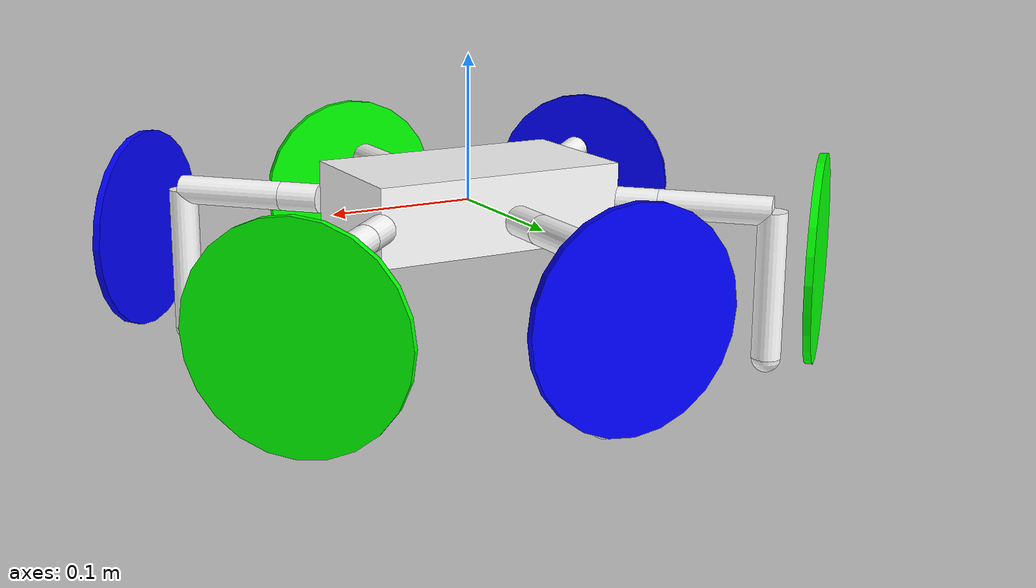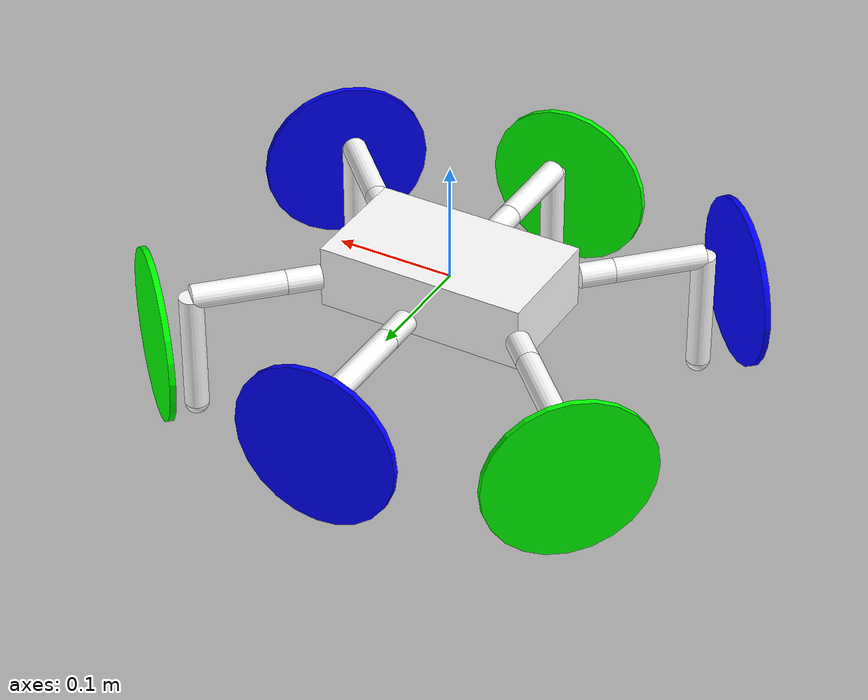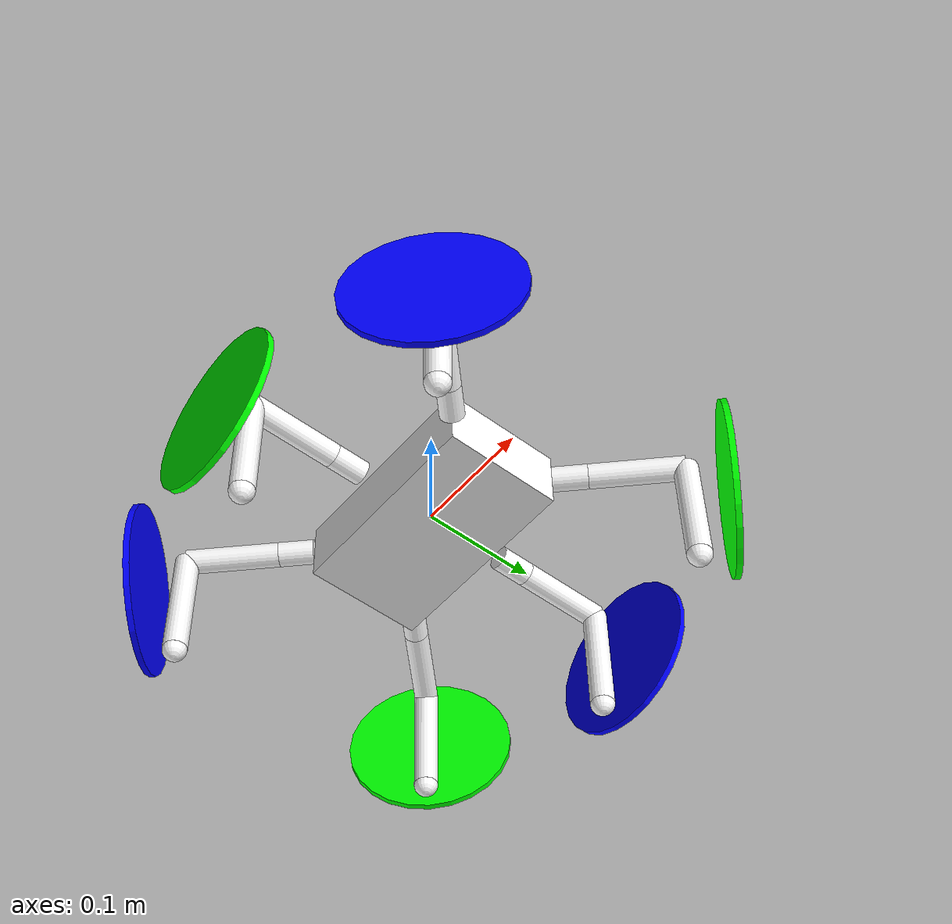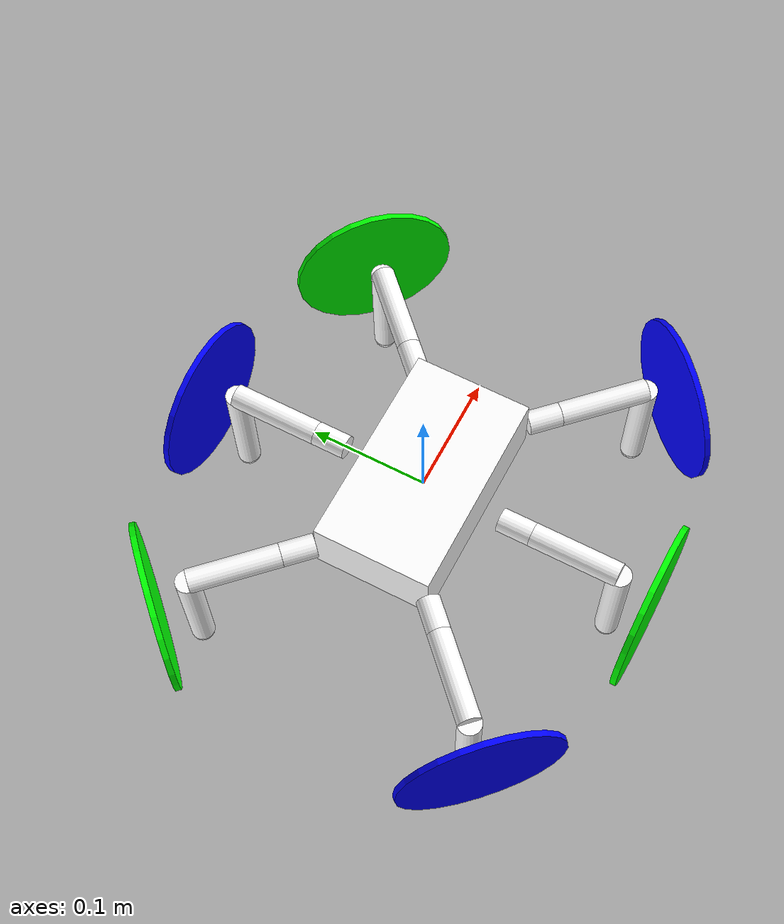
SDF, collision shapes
<sdf version="1.7">
  <model name="hexapod_copter">
    <link name="base_link">
      <inertial>
        <pose>0 0 0 0 -0 0</pose>
        <mass>0.5</mass>
        <inertia>
          <ixx>0.000542083</ixx>
          <ixy>0</ixy>
          <ixz>0</ixz>
          <iyy>0.00142242</iyy>
          <iyz>0</iyz>
          <izz>0.00173042</izz>
        </inertia>
      </inertial>
      <collision name="base_link_collision">
        <pose>0 0 0 0 -0 0</pose>
        <geometry>
          <box>
            <size>0.177 0.101 0.053</size>
          </box>
        </geometry>
        <surface>
          <friction>
            <ode>
              <mu2>1</mu2>
              <fdir1>1 0 0</fdir1>
              <mu1>1.0</mu1>
            </ode>
          </friction>
          <contact>
            <ode>
              <kp>1e+15</kp>
              <kd>1e+13</kd>
            </ode>
          </contact>
        </surface>
      </collision>
      <visual name="base_link_visual">
        <pose>0 0 -0.0265 0 -0 0</pose>
        <geometry>
          <mesh>
            <scale>1 1 1</scale>
            <uri>model://quadruped/meshes/hexapod_body.dae</uri>
          </mesh>
        </geometry>
        <material>
          <ambient>1 1 1</ambient>
          <diffuse>1 1 1</diffuse>
          <specular>1 1 1</specular>
          <pbr>
            <metal>
              <albedo_map>model://quadruped/materials/textures/silver_blue_metal/silver_blue_metal_diffuse.jpg</albedo_map>
              <metalness_map>model://quadruped/materials/textures/silver_blue_metal/silver_blue_metal_metallic.jpg</metalness_map>
              <normal_map>model://quadruped/materials/textures/silver_blue_metal/silver_blue_metal_normal.jpg</normal_map>
              <roughness_map>model://quadruped/materials/textures/silver_blue_metal/silver_blue_metal_roughness.jpg</roughness_map>
              <roughness>1.0</roughness>
              <metalness>1.0</metalness>
            </metal>
          </pbr>
        </material>
      </visual>
      <gravity>1</gravity>
      <velocity_decay/>
    </link>
    <joint name="coxa_bl_joint" type="revolute">
      <pose relative_to="base_link">-0.0885 0.0505 0 0 -0 2.35619</pose>
      <parent>base_link</parent>
      <child>coxa_bl_link</child>
      <axis>
        <xyz>0 0 1</xyz>
        <limit>
          <lower>-1.5708</lower>
          <upper>1.5708</upper>
          <effort>100</effort>
          <velocity>0.5</velocity>
        </limit>
        <dynamics>
          <spring_reference>0</spring_reference>
          <spring_stiffness>0</spring_stiffness>
        </dynamics>
      </axis>
      <physics>
        <ode>
          <limit>
            <cfm>0</cfm>
            <erp>0.2</erp>
          </limit>
        </ode>
      </physics>
    </joint>
    <link name="coxa_bl_link">
      <pose relative_to="coxa_bl_joint">0 0 0 0 -0 0</pose>
      <inertial>
        <pose>0.01425 0 0 0 1.5708 0</pose>
        <mass>0.1</mass>
        <inertia>
          <ixx>9.26875e-06</ixx>
          <ixy>0</ixy>
          <ixz>0</ixz>
          <iyy>9.26875e-06</iyy>
          <iyz>0</iyz>
          <izz>5e-06</izz>
        </inertia>
      </inertial>
      <collision name="coxa_bl_link_collision">
        <pose>0.01425 0 0 0 1.5708 0</pose>
        <geometry>
          <cylinder>
            <length>0.0285</length>
            <radius>0.01</radius>
          </cylinder>
        </geometry>
        <surface>
          <friction>
            <ode>
              <mu2>1</mu2>
              <fdir1>1 0 0</fdir1>
              <mu1>1.0</mu1>
            </ode>
          </friction>
          <contact>
            <ode/>
          </contact>
        </surface>
      </collision>
      <visual name="coxa_bl_link_visual">
        <pose>0 0 0.0196 0 -0 0</pose>
        <geometry>
          <mesh>
            <scale>1 1 1</scale>
            <uri>model://quadruped/meshes/hexapod_coxa_l.dae</uri>
          </mesh>
        </geometry>
        <material>
          <ambient>1 1 1</ambient>
          <diffuse>1 1 1</diffuse>
          <specular>1 1 1</specular>
          <pbr>
            <metal>
              <albedo_map>model://quadruped/materials/textures/silver_blue_metal/silver_blue_metal_diffuse.jpg</albedo_map>
              <metalness_map>model://quadruped/materials/textures/silver_blue_metal/silver_blue_metal_metallic.jpg</metalness_map>
              <normal_map>model://quadruped/materials/textures/silver_blue_metal/silver_blue_metal_normal.jpg</normal_map>
              <roughness_map>model://quadruped/materials/textures/silver_blue_metal/silver_blue_metal_roughness.jpg</roughness_map>
              <roughness>1.0</roughness>
              <metalness>1.0</metalness>
            </metal>
          </pbr>
        </material>
      </visual>
      <gravity>1</gravity>
      <velocity_decay/>
    </link>
    <joint name="femur_bl_joint" type="revolute">
      <pose relative_to="coxa_bl_link">0.0285 0 0 0 -0 0</pose>
      <parent>coxa_bl_link</parent>
      <child>femur_bl_link</child>
      <axis>
        <xyz>0 1 0</xyz>
        <limit>
          <lower>-1.5708</lower>
          <upper>1.5708</upper>
          <effort>100</effort>
          <velocity>0.5</velocity>
        </limit>
        <dynamics>
          <spring_reference>0</spring_reference>
          <spring_stiffness>0</spring_stiffness>
        </dynamics>
      </axis>
      <physics>
        <ode>
          <limit>
            <cfm>0</cfm>
            <erp>0.2</erp>
          </limit>
        </ode>
      </physics>
    </joint>
    <link name="femur_bl_link">
      <pose relative_to="femur_bl_joint">0 0 0 0 -0 0</pose>
      <inertial>
        <pose>0.0381 0 0 0 1.5708 0</pose>
        <mass>0.1</mass>
        <inertia>
          <ixx>5.0887e-05</ixx>
          <ixy>0</ixy>
          <ixz>0</ixz>
          <iyy>5.0887e-05</iyy>
          <iyz>0</iyz>
          <izz>5e-06</izz>
        </inertia>
      </inertial>
      <collision name="femur_bl_link_collision">
        <pose>0.0381 0 0 0 1.5708 0</pose>
        <geometry>
          <cylinder>
            <length>0.0762</length>
            <radius>0.01</radius>
          </cylinder>
        </geometry>
        <surface>
          <friction>
            <ode>
              <mu2>1</mu2>
              <fdir1>1 0 0</fdir1>
              <mu1>1.0</mu1>
            </ode>
          </friction>
          <contact>
            <ode/>
          </contact>
        </surface>
      </collision>
      <visual name="femur_bl_link_visual">
        <pose>0 -0.026 0 0 -0 0</pose>
        <geometry>
          <mesh>
            <scale>1 1 1</scale>
            <uri>model://quadruped/meshes/hexapod_femur_l.dae</uri>
          </mesh>
        </geometry>
        <material>
          <ambient>1 1 1</ambient>
          <diffuse>1 1 1</diffuse>
          <specular>1 1 1</specular>
          <pbr>
            <metal>
              <albedo_map>model://quadruped/materials/textures/silver_blue_metal/silver_blue_metal_diffuse.jpg</albedo_map>
              <metalness_map>model://quadruped/materials/textures/silver_blue_metal/silver_blue_metal_metallic.jpg</metalness_map>
              <normal_map>model://quadruped/materials/textures/silver_blue_metal/silver_blue_metal_normal.jpg</normal_map>
              <roughness_map>model://quadruped/materials/textures/silver_blue_metal/silver_blue_metal_roughness.jpg</roughness_map>
              <roughness>1.0</roughness>
              <metalness>1.0</metalness>
            </metal>
          </pbr>
        </material>
      </visual>
      <gravity>1</gravity>
      <velocity_decay/>
    </link>
    <joint name="tibia_bl_joint" type="revolute">
      <pose relative_to="femur_bl_link">0.0762 0 0 0 -0 0</pose>
      <parent>femur_bl_link</parent>
      <child>tibia_bl_link</child>
      <axis>
        <xyz>0 1 0</xyz>
        <limit>
          <lower>-1.5708</lower>
          <upper>1.5708</upper>
          <effort>100</effort>
          <velocity>0.5</velocity>
        </limit>
        <dynamics>
          <spring_reference>0</spring_reference>
          <spring_stiffness>0</spring_stiffness>
        </dynamics>
      </axis>
      <physics>
        <ode>
          <limit>
            <cfm>0</cfm>
            <erp>0.2</erp>
          </limit>
        </ode>
      </physics>
    </joint>
    <link name="tibia_bl_link">
      <pose relative_to="tibia_bl_joint">0 0 0 0 -0 0</pose>
      <inertial>
        <pose>0 0 -0.051 0 -0 0</pose>
        <mass>0.1</mass>
        <inertia>
          <ixx>8.92e-05</ixx>
          <ixy>0</ixy>
          <ixz>0</ixz>
          <iyy>8.92e-05</iyy>
          <iyz>0</iyz>
          <izz>5e-06</izz>
        </inertia>
      </inertial>
      <collision name="tibia_bl_link_collision">
        <pose>0 0 -0.051 0 -0 0</pose>
        <geometry>
          <cylinder>
            <length>0.102</length>
            <radius>0.01</radius>
          </cylinder>
        </geometry>
        <surface>
          <friction>
            <ode>
              <mu2>1</mu2>
              <fdir1>1 0 0</fdir1>
              <mu1>1.0</mu1>
            </ode>
          </friction>
          <contact>
            <ode/>
          </contact>
        </surface>
      </collision>
      <collision name="tibia_bl_link_fixed_joint_lump__foot_bl_link_collision_1">
        <pose>0 0 -0.102 0 -0 0</pose>
        <geometry>
          <sphere>
            <radius>0.01</radius>
          </sphere>
        </geometry>
        <surface>
          <friction>
            <ode>
              <mu2>1</mu2>
              <fdir1>1 0 0</fdir1>
              <mu1>1.0</mu1>
            </ode>
            <torsional>
              <coefficient>1</coefficient>
              <surface_radius>0.01</surface_radius>
              <use_patch_radius>0</use_patch_radius>
            </torsional>
          </friction>
          <contact>
            <ode>
              <kp>1e+15</kp>
              <kd>1e+13</kd>
            </ode>
          </contact>
        </surface>
      </collision>
      <visual name="tibia_bl_link_visual">
        <pose>0 -0.0185 0 0 -0 0</pose>
        <geometry>
          <mesh>
            <scale>1 1 1</scale>
            <uri>model://quadruped/meshes/hexapod_tibia_l.dae</uri>
          </mesh>
        </geometry>
        <material>
          <ambient>1 1 1</ambient>
          <diffuse>1 1 1</diffuse>
          <specular>1 1 1</specular>
          <pbr>
            <metal>
              <albedo_map>model://quadruped/materials/textures/silver_blue_metal/silver_blue_metal_diffuse.jpg</albedo_map>
              <metalness_map>model://quadruped/materials/textures/silver_blue_metal/silver_blue_metal_metallic.jpg</metalness_map>
              <normal_map>model://quadruped/materials/textures/silver_blue_metal/silver_blue_metal_normal.jpg</normal_map>
              <roughness_map>model://quadruped/materials/textures/silver_blue_metal/silver_blue_metal_roughness.jpg</roughness_map>
              <roughness>1.0</roughness>
              <metalness>1.0</metalness>
            </metal>
          </pbr>
        </material>
      </visual>
      <velocity_decay/>
      <gravity>1</gravity>
      <velocity_decay/>
    </link>
    <joint name="coxa_br_joint" type="revolute">
      <pose relative_to="base_link">-0.0885 -0.0505 0 0 0 -2.35619</pose>
      <parent>base_link</parent>
      <child>coxa_br_link</child>
      <axis>
        <xyz>0 0 1</xyz>
        <limit>
          <lower>-1.5708</lower>
          <upper>1.5708</upper>
          <effort>100</effort>
          <velocity>0.5</velocity>
        </limit>
        <dynamics>
          <spring_reference>0</spring_reference>
          <spring_stiffness>0</spring_stiffness>
        </dynamics>
      </axis>
      <physics>
        <ode>
          <limit>
            <cfm>0</cfm>
            <erp>0.2</erp>
          </limit>
        </ode>
      </physics>
    </joint>
    <link name="coxa_br_link">
      <pose relative_to="coxa_br_joint">0 0 0 0 -0 0</pose>
      <inertial>
        <pose>0.01425 0 0 0 1.5708 0</pose>
        <mass>0.1</mass>
        <inertia>
          <ixx>9.26875e-06</ixx>
          <ixy>0</ixy>
          <ixz>0</ixz>
          <iyy>9.26875e-06</iyy>
          <iyz>0</iyz>
          <izz>5e-06</izz>
        </inertia>
      </inertial>
      <collision name="coxa_br_link_collision">
        <pose>0.01425 0 0 0 1.5708 0</pose>
        <geometry>
          <cylinder>
            <length>0.0285</length>
            <radius>0.01</radius>
          </cylinder>
        </geometry>
        <surface>
          <friction>
            <ode>
              <mu2>1</mu2>
              <fdir1>1 0 0</fdir1>
              <mu1>1.0</mu1>
            </ode>
          </friction>
          <contact>
            <ode/>
          </contact>
        </surface>
      </collision>
      <visual name="coxa_br_link_visual">
        <pose>0 0 0.0196 0 -0 0</pose>
        <geometry>
          <mesh>
            <scale>1 1 1</scale>
            <uri>model://quadruped/meshes/hexapod_coxa_r.dae</uri>
          </mesh>
        </geometry>
        <material>
          <ambient>1 1 1</ambient>
          <diffuse>1 1 1</diffuse>
          <specular>1 1 1</specular>
          <pbr>
            <metal>
              <albedo_map>model://quadruped/materials/textures/silver_blue_metal/silver_blue_metal_diffuse.jpg</albedo_map>
              <metalness_map>model://quadruped/materials/textures/silver_blue_metal/silver_blue_metal_metallic.jpg</metalness_map>
              <normal_map>model://quadruped/materials/textures/silver_blue_metal/silver_blue_metal_normal.jpg</normal_map>
              <roughness_map>model://quadruped/materials/textures/silver_blue_metal/silver_blue_metal_roughness.jpg</roughness_map>
              <roughness>1.0</roughness>
              <metalness>1.0</metalness>
            </metal>
          </pbr>
        </material>
      </visual>
      <gravity>1</gravity>
      <velocity_decay/>
    </link>
    <joint name="femur_br_joint" type="revolute">
      <pose relative_to="coxa_br_link">0.0285 0 0 0 -0 0</pose>
      <parent>coxa_br_link</parent>
      <child>femur_br_link</child>
      <axis>
        <xyz>0 1 0</xyz>
        <limit>
          <lower>-1.5708</lower>
          <upper>1.5708</upper>
          <effort>100</effort>
          <velocity>0.5</velocity>
        </limit>
        <dynamics>
          <spring_reference>0</spring_reference>
          <spring_stiffness>0</spring_stiffness>
        </dynamics>
      </axis>
      <physics>
        <ode>
          <limit>
            <cfm>0</cfm>
            <erp>0.2</erp>
          </limit>
        </ode>
      </physics>
    </joint>
    <link name="femur_br_link">
      <pose relative_to="femur_br_joint">0 0 0 0 -0 0</pose>
      <inertial>
        <pose>0.0381 0 0 0 1.5708 0</pose>
        <mass>0.1</mass>
        <inertia>
          <ixx>5.0887e-05</ixx>
          <ixy>0</ixy>
          <ixz>0</ixz>
          <iyy>5.0887e-05</iyy>
          <iyz>0</iyz>
          <izz>5e-06</izz>
        </inertia>
      </inertial>
      <collision name="femur_br_link_collision">
        <pose>0.0381 0 0 0 1.5708 0</pose>
        <geometry>
          <cylinder>
            <length>0.0762</length>
            <radius>0.01</radius>
          </cylinder>
        </geometry>
        <surface>
          <friction>
            <ode>
              <mu2>1</mu2>
              <fdir1>1 0 0</fdir1>
              <mu1>1.0</mu1>
            </ode>
          </friction>
          <contact>
            <ode/>
          </contact>
        </surface>
      </collision>
      <visual name="femur_br_link_visual">
        <pose>0 0.026 0 0 -0 0</pose>
        <geometry>
          <mesh>
            <scale>1 1 1</scale>
            <uri>model://quadruped/meshes/hexapod_femur_r.dae</uri>
          </mesh>
        </geometry>
        <material>
          <ambient>1 1 1</ambient>
          <diffuse>1 1 1</diffuse>
          <specular>1 1 1</specular>
          <pbr>
            <metal>
              <albedo_map>model://quadruped/materials/textures/silver_blue_metal/silver_blue_metal_diffuse.jpg</albedo_map>
              <metalness_map>model://quadruped/materials/textures/silver_blue_metal/silver_blue_metal_metallic.jpg</metalness_map>
              <normal_map>model://quadruped/materials/textures/silver_blue_metal/silver_blue_metal_normal.jpg</normal_map>
              <roughness_map>model://quadruped/materials/textures/silver_blue_metal/silver_blue_metal_roughness.jpg</roughness_map>
              <roughness>1.0</roughness>
              <metalness>1.0</metalness>
            </metal>
          </pbr>
        </material>
      </visual>
      <gravity>1</gravity>
      <velocity_decay/>
    </link>
    <joint name="tibia_br_joint" type="revolute">
      <pose relative_to="femur_br_link">0.0762 0 0 0 -0 0</pose>
      <parent>femur_br_link</parent>
      <child>tibia_br_link</child>
      <axis>
        <xyz>0 1 0</xyz>
        <limit>
          <lower>-1.5708</lower>
          <upper>1.5708</upper>
          <effort>100</effort>
          <velocity>0.5</velocity>
        </limit>
        <dynamics>
          <spring_reference>0</spring_reference>
          <spring_stiffness>0</spring_stiffness>
        </dynamics>
      </axis>
      <physics>
        <ode>
          <limit>
            <cfm>0</cfm>
            <erp>0.2</erp>
          </limit>
        </ode>
      </physics>
    </joint>
    <link name="tibia_br_link">
      <pose relative_to="tibia_br_joint">0 0 0 0 -0 0</pose>
      <inertial>
        <pose>0 0 -0.051 0 -0 0</pose>
        <mass>0.1</mass>
        <inertia>
          <ixx>8.92e-05</ixx>
          <ixy>0</ixy>
          <ixz>0</ixz>
          <iyy>8.92e-05</iyy>
          <iyz>0</iyz>
          <izz>5e-06</izz>
        </inertia>
      </inertial>
      <collision name="tibia_br_link_collision">
        <pose>0 0 -0.051 0 -0 0</pose>
        <geometry>
          <cylinder>
            <length>0.102</length>
            <radius>0.01</radius>
          </cylinder>
        </geometry>
        <surface>
          <friction>
            <ode>
              <mu2>1</mu2>
              <fdir1>1 0 0</fdir1>
              <mu1>1.0</mu1>
            </ode>
          </friction>
          <contact>
            <ode/>
          </contact>
        </surface>
      </collision>
      <collision name="tibia_br_link_fixed_joint_lump__foot_br_link_collision_1">
        <pose>0 0 -0.102 0 -0 0</pose>
        <geometry>
          <sphere>
            <radius>0.01</radius>
          </sphere>
        </geometry>
        <surface>
          <friction>
            <ode>
              <mu2>1</mu2>
              <fdir1>1 0 0</fdir1>
              <mu1>1.0</mu1>
            </ode>
            <torsional>
              <coefficient>1</coefficient>
              <surface_radius>0.01</surface_radius>
              <use_patch_radius>0</use_patch_radius>
            </torsional>
          </friction>
          <contact>
            <ode>
              <kp>1e+15</kp>
              <kd>1e+13</kd>
            </ode>
          </contact>
        </surface>
      </collision>
      <visual name="tibia_br_link_visual">
        <pose>0 0.0185 0 0 -0 0</pose>
        <geometry>
          <mesh>
            <scale>1 1 1</scale>
            <uri>model://quadruped/meshes/hexapod_tibia_r.dae</uri>
          </mesh>
        </geometry>
        <material>
          <ambient>1 1 1</ambient>
          <diffuse>1 1 1</diffuse>
          <specular>1 1 1</specular>
          <pbr>
            <metal>
              <albedo_map>model://quadruped/materials/textures/silver_blue_metal/silver_blue_metal_diffuse.jpg</albedo_map>
              <metalness_map>model://quadruped/materials/textures/silver_blue_metal/silver_blue_metal_metallic.jpg</metalness_map>
              <normal_map>model://quadruped/materials/textures/silver_blue_metal/silver_blue_metal_normal.jpg</normal_map>
              <roughness_map>model://quadruped/materials/textures/silver_blue_metal/silver_blue_metal_roughness.jpg</roughness_map>
              <roughness>1.0</roughness>
              <metalness>1.0</metalness>
            </metal>
          </pbr>
        </material>
      </visual>
      <velocity_decay/>
      <gravity>1</gravity>
      <velocity_decay/>
    </link>
    <joint name="coxa_fl_joint" type="revolute">
      <pose relative_to="base_link">0.0885 0.0505 0 0 -0 0.785398</pose>
      <parent>base_link</parent>
      <child>coxa_fl_link</child>
      <axis>
        <xyz>0 0 1</xyz>
        <limit>
          <lower>-1.5708</lower>
          <upper>1.5708</upper>
          <effort>100</effort>
          <velocity>0.5</velocity>
        </limit>
        <dynamics>
          <spring_reference>0</spring_reference>
          <spring_stiffness>0</spring_stiffness>
        </dynamics>
      </axis>
      <physics>
        <ode>
          <limit>
            <cfm>0</cfm>
            <erp>0.2</erp>
          </limit>
        </ode>
      </physics>
    </joint>
    <link name="coxa_fl_link">
      <pose relative_to="coxa_fl_joint">0 0 0 0 -0 0</pose>
      <inertial>
        <pose>0.01425 0 0 0 1.5708 0</pose>
        <mass>0.1</mass>
        <inertia>
          <ixx>9.26875e-06</ixx>
          <ixy>0</ixy>
          <ixz>0</ixz>
          <iyy>9.26875e-06</iyy>
          <iyz>0</iyz>
          <izz>5e-06</izz>
        </inertia>
      </inertial>
      <collision name="coxa_fl_link_collision">
        <pose>0.01425 0 0 0 1.5708 0</pose>
        <geometry>
          <cylinder>
            <length>0.0285</length>
            <radius>0.01</radius>
          </cylinder>
        </geometry>
        <surface>
          <friction>
            <ode>
              <mu2>1</mu2>
              <fdir1>1 0 0</fdir1>
              <mu1>1.0</mu1>
            </ode>
          </friction>
          <contact>
            <ode/>
          </contact>
        </surface>
      </collision>
      <visual name="coxa_fl_link_visual">
        <pose>0 0 0.0196 0 -0 0</pose>
        <geometry>
          <mesh>
            <scale>1 1 1</scale>
            <uri>model://quadruped/meshes/hexapod_coxa_l.dae</uri>
          </mesh>
        </geometry>
        <material>
          <ambient>1 1 1</ambient>
          <diffuse>1 1 1</diffuse>
          <specular>1 1 1</specular>
          <pbr>
            <metal>
              <albedo_map>model://quadruped/materials/textures/silver_blue_metal/silver_blue_metal_diffuse.jpg</albedo_map>
              <metalness_map>model://quadruped/materials/textures/silver_blue_metal/silver_blue_metal_metallic.jpg</metalness_map>
              <normal_map>model://quadruped/materials/textures/silver_blue_metal/silver_blue_metal_normal.jpg</normal_map>
              <roughness_map>model://quadruped/materials/textures/silver_blue_metal/silver_blue_metal_roughness.jpg</roughness_map>
              <roughness>1.0</roughness>
              <metalness>1.0</metalness>
            </metal>
          </pbr>
        </material>
      </visual>
      <gravity>1</gravity>
      <velocity_decay/>
    </link>
    <joint name="femur_fl_joint" type="revolute">
      <pose relative_to="coxa_fl_link">0.0285 0 0 0 -0 0</pose>
      <parent>coxa_fl_link</parent>
      <child>femur_fl_link</child>
      <axis>
        <xyz>0 1 0</xyz>
        <limit>
          <lower>-1.5708</lower>
          <upper>1.5708</upper>
          <effort>100</effort>
          <velocity>0.5</velocity>
        </limit>
        <dynamics>
          <spring_reference>0</spring_reference>
          <spring_stiffness>0</spring_stiffness>
        </dynamics>
      </axis>
      <physics>
        <ode>
          <limit>
            <cfm>0</cfm>
            <erp>0.2</erp>
          </limit>
        </ode>
      </physics>
    </joint>
    <link name="femur_fl_link">
      <pose relative_to="femur_fl_joint">0 0 0 0 -0 0</pose>
      <inertial>
        <pose>0.0381 0 0 0 1.5708 0</pose>
        <mass>0.1</mass>
        <inertia>
          <ixx>5.0887e-05</ixx>
          <ixy>0</ixy>
          <ixz>0</ixz>
          <iyy>5.0887e-05</iyy>
          <iyz>0</iyz>
          <izz>5e-06</izz>
        </inertia>
      </inertial>
      <collision name="femur_fl_link_collision">
        <pose>0.0381 0 0 0 1.5708 0</pose>
        <geometry>
          <cylinder>
            <length>0.0762</length>
            <radius>0.01</radius>
          </cylinder>
        </geometry>
        <surface>
          <friction>
            <ode>
              <mu2>1</mu2>
              <fdir1>1 0 0</fdir1>
              <mu1>1.0</mu1>
            </ode>
          </friction>
          <contact>
            <ode/>
          </contact>
        </surface>
      </collision>
      <visual name="femur_fl_link_visual">
        <pose>0 -0.026 0 0 -0 0</pose>
        <geometry>
          <mesh>
            <scale>1 1 1</scale>
            <uri>model://quadruped/meshes/hexapod_femur_l.dae</uri>
          </mesh>
        </geometry>
        <material>
          <ambient>1 1 1</ambient>
          <diffuse>1 1 1</diffuse>
          <specular>1 1 1</specular>
          <pbr>
            <metal>
              <albedo_map>model://quadruped/materials/textures/silver_blue_metal/silver_blue_metal_diffuse.jpg</albedo_map>
              <metalness_map>model://quadruped/materials/textures/silver_blue_metal/silver_blue_metal_metallic.jpg</metalness_map>
              <normal_map>model://quadruped/materials/textures/silver_blue_metal/silver_blue_metal_normal.jpg</normal_map>
              <roughness_map>model://quadruped/materials/textures/silver_blue_metal/silver_blue_metal_roughness.jpg</roughness_map>
              <roughness>1.0</roughness>
              <metalness>1.0</metalness>
            </metal>
          </pbr>
        </material>
      </visual>
      <gravity>1</gravity>
      <velocity_decay/>
    </link>
    <joint name="tibia_fl_joint" type="revolute">
      <pose relative_to="femur_fl_link">0.0762 0 0 0 -0 0</pose>
      <parent>femur_fl_link</parent>
      <child>tibia_fl_link</child>
      <axis>
        <xyz>0 1 0</xyz>
        <limit>
          <lower>-1.5708</lower>
          <upper>1.5708</upper>
          <effort>100</effort>
          <velocity>0.5</velocity>
        </limit>
        <dynamics>
          <spring_reference>0</spring_reference>
          <spring_stiffness>0</spring_stiffness>
        </dynamics>
      </axis>
      <physics>
        <ode>
          <limit>
            <cfm>0</cfm>
            <erp>0.2</erp>
          </limit>
        </ode>
      </physics>
    </joint>
    <link name="tibia_fl_link">
      <pose relative_to="tibia_fl_joint">0 0 0 0 -0 0</pose>
      <inertial>
        <pose>0 0 -0.051 0 -0 0</pose>
        <mass>0.1</mass>
        <inertia>
          <ixx>8.92e-05</ixx>
          <ixy>0</ixy>
          <ixz>0</ixz>
          <iyy>8.92e-05</iyy>
          <iyz>0</iyz>
          <izz>5e-06</izz>
        </inertia>
      </inertial>
      <collision name="tibia_fl_link_collision">
        <pose>0 0 -0.051 0 -0 0</pose>
        <geometry>
          <cylinder>
            <length>0.102</length>
            <radius>0.01</radius>
          </cylinder>
        </geometry>
        <surface>
          <friction>
            <ode>
              <mu2>1</mu2>
              <fdir1>1 0 0</fdir1>
              <mu1>1.0</mu1>
            </ode>
          </friction>
          <contact>
            <ode/>
          </contact>
        </surface>
      </collision>
      <collision name="tibia_fl_link_fixed_joint_lump__foot_fl_link_collision_1">
        <pose>0 0 -0.102 0 -0 0</pose>
        <geometry>
          <sphere>
            <radius>0.01</radius>
          </sphere>
        </geometry>
        <surface>
          <friction>
            <ode>
              <mu2>1</mu2>
              <fdir1>1 0 0</fdir1>
              <mu1>1.0</mu1>
            </ode>
            <torsional>
              <coefficient>1</coefficient>
              <surface_radius>0.01</surface_radius>
              <use_patch_radius>0</use_patch_radius>
            </torsional>
          </friction>
          <contact>
            <ode>
              <kp>1e+15</kp>
              <kd>1e+13</kd>
            </ode>
          </contact>
        </surface>
      </collision>
      <visual name="tibia_fl_link_visual">
        <pose>0 -0.0185 0 0 -0 0</pose>
        <geometry>
          <mesh>
            <scale>1 1 1</scale>
            <uri>model://quadruped/meshes/hexapod_tibia_l.dae</uri>
          </mesh>
        </geometry>
        <material>
          <ambient>1 1 1</ambient>
          <diffuse>1 1 1</diffuse>
          <specular>1 1 1</specular>
          <pbr>
            <metal>
              <albedo_map>model://quadruped/materials/textures/silver_blue_metal/silver_blue_metal_diffuse.jpg</albedo_map>
              <metalness_map>model://quadruped/materials/textures/silver_blue_metal/silver_blue_metal_metallic.jpg</metalness_map>
              <normal_map>model://quadruped/materials/textures/silver_blue_metal/silver_blue_metal_normal.jpg</normal_map>
              <roughness_map>model://quadruped/materials/textures/silver_blue_metal/silver_blue_metal_roughness.jpg</roughness_map>
              <roughness>1.0</roughness>
              <metalness>1.0</metalness>
            </metal>
          </pbr>
        </material>
      </visual>
      <velocity_decay/>
      <gravity>1</gravity>
      <velocity_decay/>
    </link>
    <joint name="coxa_fr_joint" type="revolute">
      <pose relative_to="base_link">0.0885 -0.0505 0 0 0 -0.785398</pose>
      <parent>base_link</parent>
      <child>coxa_fr_link</child>
      <axis>
        <xyz>0 0 1</xyz>
        <limit>
          <lower>-1.5708</lower>
          <upper>1.5708</upper>
          <effort>100</effort>
          <velocity>0.5</velocity>
        </limit>
        <dynamics>
          <spring_reference>0</spring_reference>
          <spring_stiffness>0</spring_stiffness>
        </dynamics>
      </axis>
      <physics>
        <ode>
          <limit>
            <cfm>0</cfm>
            <erp>0.2</erp>
          </limit>
        </ode>
      </physics>
    </joint>
    <link name="coxa_fr_link">
      <pose relative_to="coxa_fr_joint">0 0 0 0 -0 0</pose>
      <inertial>
        <pose>0.01425 0 0 0 1.5708 0</pose>
        <mass>0.1</mass>
        <inertia>
          <ixx>9.26875e-06</ixx>
          <ixy>0</ixy>
          <ixz>0</ixz>
          <iyy>9.26875e-06</iyy>
          <iyz>0</iyz>
          <izz>5e-06</izz>
        </inertia>
      </inertial>
      <collision name="coxa_fr_link_collision">
        <pose>0.01425 0 0 0 1.5708 0</pose>
        <geometry>
          <cylinder>
            <length>0.0285</length>
            <radius>0.01</radius>
          </cylinder>
        </geometry>
        <surface>
          <friction>
            <ode>
              <mu2>1</mu2>
              <fdir1>1 0 0</fdir1>
              <mu1>1.0</mu1>
            </ode>
          </friction>
          <contact>
            <ode/>
          </contact>
        </surface>
      </collision>
      <visual name="coxa_fr_link_visual">
        <pose>0 0 0.0196 0 -0 0</pose>
        <geometry>
          <mesh>
            <scale>1 1 1</scale>
            <uri>model://quadruped/meshes/hexapod_coxa_r.dae</uri>
          </mesh>
        </geometry>
        <material>
          <ambient>1 1 1</ambient>
          <diffuse>1 1 1</diffuse>
          <specular>1 1 1</specular>
          <pbr>
            <metal>
              <albedo_map>model://quadruped/materials/textures/silver_blue_metal/silver_blue_metal_diffuse.jpg</albedo_map>
              <metalness_map>model://quadruped/materials/textures/silver_blue_metal/silver_blue_metal_metallic.jpg</metalness_map>
              <normal_map>model://quadruped/materials/textures/silver_blue_metal/silver_blue_metal_normal.jpg</normal_map>
              <roughness_map>model://quadruped/materials/textures/silver_blue_metal/silver_blue_metal_roughness.jpg</roughness_map>
              <roughness>1.0</roughness>
              <metalness>1.0</metalness>
            </metal>
          </pbr>
        </material>
      </visual>
      <gravity>1</gravity>
      <velocity_decay/>
    </link>
    <joint name="femur_fr_joint" type="revolute">
      <pose relative_to="coxa_fr_link">0.0285 0 0 0 -0 0</pose>
      <parent>coxa_fr_link</parent>
      <child>femur_fr_link</child>
      <axis>
        <xyz>0 1 0</xyz>
        <limit>
          <lower>-1.5708</lower>
          <upper>1.5708</upper>
          <effort>100</effort>
          <velocity>0.5</velocity>
        </limit>
        <dynamics>
          <spring_reference>0</spring_reference>
          <spring_stiffness>0</spring_stiffness>
        </dynamics>
      </axis>
      <physics>
        <ode>
          <limit>
            <cfm>0</cfm>
            <erp>0.2</erp>
          </limit>
        </ode>
      </physics>
    </joint>
    <link name="femur_fr_link">
      <pose relative_to="femur_fr_joint">0 0 0 0 -0 0</pose>
      <inertial>
        <pose>0.0381 0 0 0 1.5708 0</pose>
        <mass>0.1</mass>
        <inertia>
          <ixx>5.0887e-05</ixx>
          <ixy>0</ixy>
          <ixz>0</ixz>
          <iyy>5.0887e-05</iyy>
          <iyz>0</iyz>
          <izz>5e-06</izz>
        </inertia>
      </inertial>
      <collision name="femur_fr_link_collision">
        <pose>0.0381 0 0 0 1.5708 0</pose>
        <geometry>
          <cylinder>
            <length>0.0762</length>
            <radius>0.01</radius>
          </cylinder>
        </geometry>
        <surface>
          <friction>
            <ode>
              <mu2>1</mu2>
              <fdir1>1 0 0</fdir1>
              <mu1>1.0</mu1>
            </ode>
          </friction>
          <contact>
            <ode/>
          </contact>
        </surface>
      </collision>
      <visual name="femur_fr_link_visual">
        <pose>0 0.026 0 0 -0 0</pose>
        <geometry>
          <mesh>
            <scale>1 1 1</scale>
            <uri>model://quadruped/meshes/hexapod_femur_r.dae</uri>
          </mesh>
        </geometry>
        <material>
          <ambient>1 1 1</ambient>
          <diffuse>1 1 1</diffuse>
          <specular>1 1 1</specular>
          <pbr>
            <metal>
              <albedo_map>model://quadruped/materials/textures/silver_blue_metal/silver_blue_metal_diffuse.jpg</albedo_map>
              <metalness_map>model://quadruped/materials/textures/silver_blue_metal/silver_blue_metal_metallic.jpg</metalness_map>
              <normal_map>model://quadruped/materials/textures/silver_blue_metal/silver_blue_metal_normal.jpg</normal_map>
              <roughness_map>model://quadruped/materials/textures/silver_blue_metal/silver_blue_metal_roughness.jpg</roughness_map>
              <roughness>1.0</roughness>
              <metalness>1.0</metalness>
            </metal>
          </pbr>
        </material>
      </visual>
      <gravity>1</gravity>
      <velocity_decay/>
    </link>
    <joint name="tibia_fr_joint" type="revolute">
      <pose relative_to="femur_fr_link">0.0762 0 0 0 -0 0</pose>
      <parent>femur_fr_link</parent>
      <child>tibia_fr_link</child>
      <axis>
        <xyz>0 1 0</xyz>
        <limit>
          <lower>-1.5708</lower>
          <upper>1.5708</upper>
          <effort>100</effort>
          <velocity>0.5</velocity>
        </limit>
        <dynamics>
          <spring_reference>0</spring_reference>
          <spring_stiffness>0</spring_stiffness>
        </dynamics>
      </axis>
      <physics>
        <ode>
          <limit>
            <cfm>0</cfm>
            <erp>0.2</erp>
          </limit>
        </ode>
      </physics>
    </joint>
    <link name="tibia_fr_link">
      <pose relative_to="tibia_fr_joint">0 0 0 0 -0 0</pose>
      <inertial>
        <pose>0 0 -0.051 0 -0 0</pose>
        <mass>0.1</mass>
        <inertia>
          <ixx>8.92e-05</ixx>
          <ixy>0</ixy>
          <ixz>0</ixz>
          <iyy>8.92e-05</iyy>
          <iyz>0</iyz>
          <izz>5e-06</izz>
        </inertia>
      </inertial>
      <collision name="tibia_fr_link_collision">
        <pose>0 0 -0.051 0 -0 0</pose>
        <geometry>
          <cylinder>
            <length>0.102</length>
            <radius>0.01</radius>
          </cylinder>
        </geometry>
        <surface>
          <friction>
            <ode>
              <mu2>1</mu2>
              <fdir1>1 0 0</fdir1>
              <mu1>1.0</mu1>
            </ode>
          </friction>
          <contact>
            <ode/>
          </contact>
        </surface>
      </collision>
      <collision name="tibia_fr_link_fixed_joint_lump__foot_fr_link_collision_1">
        <pose>0 0 -0.102 0 -0 0</pose>
        <geometry>
          <sphere>
            <radius>0.01</radius>
          </sphere>
        </geometry>
        <surface>
          <friction>
            <ode>
              <mu2>1</mu2>
              <fdir1>1 0 0</fdir1>
              <mu1>1.0</mu1>
            </ode>
            <torsional>
              <coefficient>1</coefficient>
              <surface_radius>0.01</surface_radius>
              <use_patch_radius>0</use_patch_radius>
            </torsional>
          </friction>
          <contact>
            <ode>
              <kp>1e+15</kp>
              <kd>1e+13</kd>
            </ode>
          </contact>
        </surface>
      </collision>
      <visual name="tibia_fr_link_visual">
        <pose>0 0.0185 0 0 -0 0</pose>
        <geometry>
          <mesh>
            <scale>1 1 1</scale>
            <uri>model://quadruped/meshes/hexapod_tibia_r.dae</uri>
          </mesh>
        </geometry>
        <material>
          <ambient>1 1 1</ambient>
          <diffuse>1 1 1</diffuse>
          <specular>1 1 1</specular>
          <pbr>
            <metal>
              <albedo_map>model://quadruped/materials/textures/silver_blue_metal/silver_blue_metal_diffuse.jpg</albedo_map>
              <metalness_map>model://quadruped/materials/textures/silver_blue_metal/silver_blue_metal_metallic.jpg</metalness_map>
              <normal_map>model://quadruped/materials/textures/silver_blue_metal/silver_blue_metal_normal.jpg</normal_map>
              <roughness_map>model://quadruped/materials/textures/silver_blue_metal/silver_blue_metal_roughness.jpg</roughness_map>
              <roughness>1.0</roughness>
              <metalness>1.0</metalness>
            </metal>
          </pbr>
        </material>
      </visual>
      <velocity_decay/>
      <gravity>1</gravity>
      <velocity_decay/>
    </link>

    <!-- add two more legs -->
    <joint name="coxa_ml_joint" type="revolute">
      <pose relative_to="base_link">0 0.07 0 0 0 1.570796</pose>
      <parent>base_link</parent>
      <child>coxa_ml_link</child>
      <axis>
        <xyz>0 0 1</xyz>
        <limit>
          <lower>-1.5708</lower>
          <upper>1.5708</upper>
          <effort>100</effort>
          <velocity>0.5</velocity>
        </limit>
        <dynamics>
          <spring_reference>0</spring_reference>
          <spring_stiffness>0</spring_stiffness>
        </dynamics>
      </axis>
      <physics>
        <ode>
          <limit>
            <cfm>0</cfm>
            <erp>0.2</erp>
          </limit>
        </ode>
      </physics>
    </joint>
    <link name="coxa_ml_link">
      <pose relative_to="coxa_ml_joint">0 0 0 0 -0 0</pose>
      <inertial>
        <pose>0.01425 0 0 0 1.5708 0</pose>
        <mass>0.1</mass>
        <inertia>
          <ixx>9.26875e-06</ixx>
          <ixy>0</ixy>
          <ixz>0</ixz>
          <iyy>9.26875e-06</iyy>
          <iyz>0</iyz>
          <izz>5e-06</izz>
        </inertia>
      </inertial>
      <collision name="coxa_ml_link_collision">
        <pose>0.01425 0 0 0 1.5708 0</pose>
        <geometry>
          <cylinder>
            <length>0.0285</length>
            <radius>0.01</radius>
          </cylinder>
        </geometry>
        <surface>
          <friction>
            <ode>
              <mu2>1</mu2>
              <fdir1>1 0 0</fdir1>
              <mu1>1.0</mu1>
            </ode>
          </friction>
          <contact>
            <ode/>
          </contact>
        </surface>
      </collision>
      <visual name="coxa_ml_link_visual">
        <pose>0 0 0.0196 0 -0 0</pose>
        <geometry>
          <mesh>
            <scale>1 1 1</scale>
            <uri>model://quadruped/meshes/hexapod_coxa_l.dae</uri>
          </mesh>
        </geometry>
        <material>
          <ambient>1 1 1</ambient>
          <diffuse>1 1 1</diffuse>
          <specular>1 1 1</specular>
          <pbr>
            <metal>
              <albedo_map>model://quadruped/materials/textures/silver_blue_metal/silver_blue_metal_diffuse.jpg</albedo_map>
              <metalness_map>model://quadruped/materials/textures/silver_blue_metal/silver_blue_metal_metallic.jpg</metalness_map>
              <normal_map>model://quadruped/materials/textures/silver_blue_metal/silver_blue_metal_normal.jpg</normal_map>
              <roughness_map>model://quadruped/materials/textures/silver_blue_metal/silver_blue_metal_roughness.jpg</roughness_map>
              <roughness>1.0</roughness>
              <metalness>1.0</metalness>
            </metal>
          </pbr>
        </material>
      </visual>
      <gravity>1</gravity>
      <velocity_decay/>
    </link>
    <joint name="femur_ml_joint" type="revolute">
      <pose relative_to="coxa_ml_link">0.0285 0 0 0 -0 0</pose>
      <parent>coxa_ml_link</parent>
      <child>femur_ml_link</child>
      <axis>
        <xyz>0 1 0</xyz>
        <limit>
          <lower>-1.5708</lower>
          <upper>1.5708</upper>
          <effort>100</effort>
          <velocity>0.5</velocity>
        </limit>
        <dynamics>
          <spring_reference>0</spring_reference>
          <spring_stiffness>0</spring_stiffness>
        </dynamics>
      </axis>
      <physics>
        <ode>
          <limit>
            <cfm>0</cfm>
            <erp>0.2</erp>
          </limit>
        </ode>
      </physics>
    </joint>
    <link name="femur_ml_link">
      <pose relative_to="femur_ml_joint">0 0 0 0 -0 0</pose>
      <inertial>
        <pose>0.0381 0 0 0 1.5708 0</pose>
        <mass>0.1</mass>
        <inertia>
          <ixx>5.0887e-05</ixx>
          <ixy>0</ixy>
          <ixz>0</ixz>
          <iyy>5.0887e-05</iyy>
          <iyz>0</iyz>
          <izz>5e-06</izz>
        </inertia>
      </inertial>
      <collision name="femur_ml_link_collision">
        <pose>0.0381 0 0 0 1.5708 0</pose>
        <geometry>
          <cylinder>
            <length>0.0762</length>
            <radius>0.01</radius>
          </cylinder>
        </geometry>
        <surface>
          <friction>
            <ode>
              <mu2>1</mu2>
              <fdir1>1 0 0</fdir1>
              <mu1>1.0</mu1>
            </ode>
          </friction>
          <contact>
            <ode/>
          </contact>
        </surface>
      </collision>
      <visual name="femur_ml_link_visual">
        <pose>0 -0.026 0 0 -0 0</pose>
        <geometry>
          <mesh>
            <scale>1 1 1</scale>
            <uri>model://quadruped/meshes/hexapod_femur_l.dae</uri>
          </mesh>
        </geometry>
        <material>
          <ambient>1 1 1</ambient>
          <diffuse>1 1 1</diffuse>
          <specular>1 1 1</specular>
          <pbr>
            <metal>
              <albedo_map>model://quadruped/materials/textures/silver_blue_metal/silver_blue_metal_diffuse.jpg</albedo_map>
              <metalness_map>model://quadruped/materials/textures/silver_blue_metal/silver_blue_metal_metallic.jpg</metalness_map>
              <normal_map>model://quadruped/materials/textures/silver_blue_metal/silver_blue_metal_normal.jpg</normal_map>
              <roughness_map>model://quadruped/materials/textures/silver_blue_metal/silver_blue_metal_roughness.jpg</roughness_map>
              <roughness>1.0</roughness>
              <metalness>1.0</metalness>
            </metal>
          </pbr>
        </material>
      </visual>
      <gravity>1</gravity>
      <velocity_decay/>
    </link>
    <joint name="tibia_ml_joint" type="revolute">
      <pose relative_to="femur_ml_link">0.0762 0 0 0 -0 0</pose>
      <parent>femur_ml_link</parent>
      <child>tibia_ml_link</child>
      <axis>
        <xyz>0 1 0</xyz>
        <limit>
          <lower>-1.5708</lower>
          <upper>1.5708</upper>
          <effort>100</effort>
          <velocity>0.5</velocity>
        </limit>
        <dynamics>
          <spring_reference>0</spring_reference>
          <spring_stiffness>0</spring_stiffness>
        </dynamics>
      </axis>
      <physics>
        <ode>
          <limit>
            <cfm>0</cfm>
            <erp>0.2</erp>
          </limit>
        </ode>
      </physics>
    </joint>
    <link name="tibia_ml_link">
      <pose relative_to="tibia_ml_joint">0 0 0 0 -0 0</pose>
      <inertial>
        <pose>0 0 -0.051 0 -0 0</pose>
        <mass>0.1</mass>
        <inertia>
          <ixx>8.92e-05</ixx>
          <ixy>0</ixy>
          <ixz>0</ixz>
          <iyy>8.92e-05</iyy>
          <iyz>0</iyz>
          <izz>5e-06</izz>
        </inertia>
      </inertial>
      <collision name="tibia_ml_link_collision">
        <pose>0 0 -0.051 0 -0 0</pose>
        <geometry>
          <cylinder>
            <length>0.102</length>
            <radius>0.01</radius>
          </cylinder>
        </geometry>
        <surface>
          <friction>
            <ode>
              <mu2>1</mu2>
              <fdir1>1 0 0</fdir1>
              <mu1>1.0</mu1>
            </ode>
          </friction>
          <contact>
            <ode/>
          </contact>
        </surface>
      </collision>
      <collision name="tibia_ml_link_fixed_joint_lump__foot_ml_link_collision_1">
        <pose>0 0 -0.102 0 -0 0</pose>
        <geometry>
          <sphere>
            <radius>0.01</radius>
          </sphere>
        </geometry>
        <surface>
          <friction>
            <ode>
              <mu2>1</mu2>
              <fdir1>1 0 0</fdir1>
              <mu1>1.0</mu1>
            </ode>
            <torsional>
              <coefficient>1</coefficient>
              <surface_radius>0.01</surface_radius>
              <use_patch_radius>0</use_patch_radius>
            </torsional>
          </friction>
          <contact>
            <ode>
              <kp>1e+15</kp>
              <kd>1e+13</kd>
            </ode>
          </contact>
        </surface>
      </collision>
      <visual name="tibia_ml_link_visual">
        <pose>0 -0.0185 0 0 -0 0</pose>
        <geometry>
          <mesh>
            <scale>1 1 1</scale>
            <uri>model://quadruped/meshes/hexapod_tibia_l.dae</uri>
          </mesh>
        </geometry>
        <material>
          <ambient>1 1 1</ambient>
          <diffuse>1 1 1</diffuse>
          <specular>1 1 1</specular>
          <pbr>
            <metal>
              <albedo_map>model://quadruped/materials/textures/silver_blue_metal/silver_blue_metal_diffuse.jpg</albedo_map>
              <metalness_map>model://quadruped/materials/textures/silver_blue_metal/silver_blue_metal_metallic.jpg</metalness_map>
              <normal_map>model://quadruped/materials/textures/silver_blue_metal/silver_blue_metal_normal.jpg</normal_map>
              <roughness_map>model://quadruped/materials/textures/silver_blue_metal/silver_blue_metal_roughness.jpg</roughness_map>
              <roughness>1.0</roughness>
              <metalness>1.0</metalness>
            </metal>
          </pbr>
        </material>
      </visual>
      <velocity_decay/>
      <gravity>1</gravity>
      <velocity_decay/>
    </link>

    <joint name="coxa_mr_joint" type="revolute">
      <pose relative_to="base_link">0 -0.07 0 0 0 -1.570796</pose>
      <parent>base_link</parent>
      <child>coxa_mr_link</child>
      <axis>
        <xyz>0 0 1</xyz>
        <limit>
          <lower>-1.5708</lower>
          <upper>1.5708</upper>
          <effort>100</effort>
          <velocity>0.5</velocity>
        </limit>
        <dynamics>
          <spring_reference>0</spring_reference>
          <spring_stiffness>0</spring_stiffness>
        </dynamics>
      </axis>
      <physics>
        <ode>
          <limit>
            <cfm>0</cfm>
            <erp>0.2</erp>
          </limit>
        </ode>
      </physics>
    </joint>
    <link name="coxa_mr_link">
      <pose relative_to="coxa_mr_joint">0 0 0 0 -0 0</pose>
      <inertial>
        <pose>0.01425 0 0 0 1.5708 0</pose>
        <mass>0.1</mass>
        <inertia>
          <ixx>9.26875e-06</ixx>
          <ixy>0</ixy>
          <ixz>0</ixz>
          <iyy>9.26875e-06</iyy>
          <iyz>0</iyz>
          <izz>5e-06</izz>
        </inertia>
      </inertial>
      <collision name="coxa_mr_link_collision">
        <pose>0.01425 0 0 0 1.5708 0</pose>
        <geometry>
          <cylinder>
            <length>0.0285</length>
            <radius>0.01</radius>
          </cylinder>
        </geometry>
        <surface>
          <friction>
            <ode>
              <mu2>1</mu2>
              <fdir1>1 0 0</fdir1>
              <mu1>1.0</mu1>
            </ode>
          </friction>
          <contact>
            <ode/>
          </contact>
        </surface>
      </collision>
      <visual name="coxa_mr_link_visual">
        <pose>0 0 0.0196 0 -0 0</pose>
        <geometry>
          <mesh>
            <scale>1 1 1</scale>
            <uri>model://quadruped/meshes/hexapod_coxa_r.dae</uri>
          </mesh>
        </geometry>
        <material>
          <ambient>1 1 1</ambient>
          <diffuse>1 1 1</diffuse>
          <specular>1 1 1</specular>
          <pbr>
            <metal>
              <albedo_map>model://quadruped/materials/textures/silver_blue_metal/silver_blue_metal_diffuse.jpg</albedo_map>
              <metalness_map>model://quadruped/materials/textures/silver_blue_metal/silver_blue_metal_metallic.jpg</metalness_map>
              <normal_map>model://quadruped/materials/textures/silver_blue_metal/silver_blue_metal_normal.jpg</normal_map>
              <roughness_map>model://quadruped/materials/textures/silver_blue_metal/silver_blue_metal_roughness.jpg</roughness_map>
              <roughness>1.0</roughness>
              <metalness>1.0</metalness>
            </metal>
          </pbr>
        </material>
      </visual>
      <gravity>1</gravity>
      <velocity_decay/>
    </link>
    <joint name="femur_mr_joint" type="revolute">
      <pose relative_to="coxa_mr_link">0.0285 0 0 0 -0 0</pose>
      <parent>coxa_mr_link</parent>
      <child>femur_mr_link</child>
      <axis>
        <xyz>0 1 0</xyz>
        <limit>
          <lower>-1.5708</lower>
          <upper>1.5708</upper>
          <effort>100</effort>
          <velocity>0.5</velocity>
        </limit>
        <dynamics>
          <spring_reference>0</spring_reference>
          <spring_stiffness>0</spring_stiffness>
        </dynamics>
      </axis>
      <physics>
        <ode>
          <limit>
            <cfm>0</cfm>
            <erp>0.2</erp>
          </limit>
        </ode>
      </physics>
    </joint>
    <link name="femur_mr_link">
      <pose relative_to="femur_mr_joint">0 0 0 0 -0 0</pose>
      <inertial>
        <pose>0.0381 0 0 0 1.5708 0</pose>
        <mass>0.1</mass>
        <inertia>
          <ixx>5.0887e-05</ixx>
          <ixy>0</ixy>
          <ixz>0</ixz>
          <iyy>5.0887e-05</iyy>
          <iyz>0</iyz>
          <izz>5e-06</izz>
        </inertia>
      </inertial>
      <collision name="femur_mr_link_collision">
        <pose>0.0381 0 0 0 1.5708 0</pose>
        <geometry>
          <cylinder>
            <length>0.0762</length>
            <radius>0.01</radius>
          </cylinder>
        </geometry>
        <surface>
          <friction>
            <ode>
              <mu2>1</mu2>
              <fdir1>1 0 0</fdir1>
              <mu1>1.0</mu1>
            </ode>
          </friction>
          <contact>
            <ode/>
          </contact>
        </surface>
      </collision>
      <visual name="femur_mr_link_visual">
        <pose>0 0.026 0 0 -0 0</pose>
        <geometry>
          <mesh>
            <scale>1 1 1</scale>
            <uri>model://quadruped/meshes/hexapod_femur_r.dae</uri>
          </mesh>
        </geometry>
        <material>
          <ambient>1 1 1</ambient>
          <diffuse>1 1 1</diffuse>
          <specular>1 1 1</specular>
          <pbr>
            <metal>
              <albedo_map>model://quadruped/materials/textures/silver_blue_metal/silver_blue_metal_diffuse.jpg</albedo_map>
              <metalness_map>model://quadruped/materials/textures/silver_blue_metal/silver_blue_metal_metallic.jpg</metalness_map>
              <normal_map>model://quadruped/materials/textures/silver_blue_metal/silver_blue_metal_normal.jpg</normal_map>
              <roughness_map>model://quadruped/materials/textures/silver_blue_metal/silver_blue_metal_roughness.jpg</roughness_map>
              <roughness>1.0</roughness>
              <metalness>1.0</metalness>
            </metal>
          </pbr>
        </material>
      </visual>
      <gravity>1</gravity>
      <velocity_decay/>
    </link>
    <joint name="tibia_mr_joint" type="revolute">
      <pose relative_to="femur_mr_link">0.0762 0 0 0 -0 0</pose>
      <parent>femur_mr_link</parent>
      <child>tibia_mr_link</child>
      <axis>
        <xyz>0 1 0</xyz>
        <limit>
          <lower>-1.5708</lower>
          <upper>1.5708</upper>
          <effort>100</effort>
          <velocity>0.5</velocity>
        </limit>
        <dynamics>
          <spring_reference>0</spring_reference>
          <spring_stiffness>0</spring_stiffness>
        </dynamics>
      </axis>
      <physics>
        <ode>
          <limit>
            <cfm>0</cfm>
            <erp>0.2</erp>
          </limit>
        </ode>
      </physics>
    </joint>
    <link name="tibia_mr_link">
      <pose relative_to="tibia_mr_joint">0 0 0 0 -0 0</pose>
      <inertial>
        <pose>0 0 -0.051 0 -0 0</pose>
        <mass>0.1</mass>
        <inertia>
          <ixx>8.92e-05</ixx>
          <ixy>0</ixy>
          <ixz>0</ixz>
          <iyy>8.92e-05</iyy>
          <iyz>0</iyz>
          <izz>5e-06</izz>
        </inertia>
      </inertial>
      <collision name="tibia_mr_link_collision">
        <pose>0 0 -0.051 0 -0 0</pose>
        <geometry>
          <cylinder>
            <length>0.102</length>
            <radius>0.01</radius>
          </cylinder>
        </geometry>
        <surface>
          <friction>
            <ode>
              <mu2>1</mu2>
              <fdir1>1 0 0</fdir1>
              <mu1>1.0</mu1>
            </ode>
          </friction>
          <contact>
            <ode/>
          </contact>
        </surface>
      </collision>
      <collision name="tibia_mr_link_fixed_joint_lump__foot_mr_link_collision_1">
        <pose>0 0 -0.102 0 -0 0</pose>
        <geometry>
          <sphere>
            <radius>0.01</radius>
          </sphere>
        </geometry>
        <surface>
          <friction>
            <ode>
              <mu2>1</mu2>
              <fdir1>1 0 0</fdir1>
              <mu1>1.0</mu1>
            </ode>
            <torsional>
              <coefficient>1</coefficient>
              <surface_radius>0.01</surface_radius>
              <use_patch_radius>0</use_patch_radius>
            </torsional>
          </friction>
          <contact>
            <ode>
              <kp>1e+15</kp>
              <kd>1e+13</kd>
            </ode>
          </contact>
        </surface>
      </collision>
      <visual name="tibia_mr_link_visual">
        <pose>0 0.0185 0 0 -0 0</pose>
        <geometry>
          <mesh>
            <scale>1 1 1</scale>
            <uri>model://quadruped/meshes/hexapod_tibia_r.dae</uri>
          </mesh>
        </geometry>
        <material>
          <ambient>1 1 1</ambient>
          <diffuse>1 1 1</diffuse>
          <specular>1 1 1</specular>
          <pbr>
            <metal>
              <albedo_map>model://quadruped/materials/textures/silver_blue_metal/silver_blue_metal_diffuse.jpg</albedo_map>
              <metalness_map>model://quadruped/materials/textures/silver_blue_metal/silver_blue_metal_metallic.jpg</metalness_map>
              <normal_map>model://quadruped/materials/textures/silver_blue_metal/silver_blue_metal_normal.jpg</normal_map>
              <roughness_map>model://quadruped/materials/textures/silver_blue_metal/silver_blue_metal_roughness.jpg</roughness_map>
              <roughness>1.0</roughness>
              <metalness>1.0</metalness>
            </metal>
          </pbr>
        </material>
      </visual>
      <velocity_decay/>
      <gravity>1</gravity>
      <velocity_decay/>
    </link>

    <!-- motor 3 cw front left -->
    <link name="motor3_fl_link">
      <pose relative_to="motor3_fl_joint">0 0 0 0 0 0</pose>
      <inertial>
        <mass>0.025</mass>
        <inertia>
          <ixx>9.75e-06</ixx>
          <ixy>0</ixy>
          <ixz>0</ixz>
          <iyy>0.000166704</iyy>
          <iyz>0</iyz>
          <izz>0.000167604</izz>
        </inertia>
      </inertial>
      <collision name="collision">
        <geometry>
          <cylinder>
            <length>0.005</length>
            <radius>0.07</radius>
          </cylinder>
        </geometry>
      </collision>
      <visual name="visual">
        <geometry>
          <mesh>
            <scale>0.7 0.7 0.7</scale>
            <uri>model://hexapod_copter/meshes/iris_prop_cw.dae</uri>
          </mesh>
        </geometry>
        <material>
          <ambient>0 1 0</ambient>
          <diffuse>0 1 0</diffuse>
          <specular>0.1 0.1 0.1 1</specular>
        </material>
      </visual>
    </link>
    <joint name="motor3_fl_joint" type="revolute">
      <pose relative_to="tibia_fl_link">0.03 0 -0.03 0 1.570796 0</pose>
      <child>motor3_fl_link</child>
      <parent>tibia_fl_link</parent>
      <axis>
        <xyz>0 0 1</xyz>
        <limit>
          <lower>-1e+16</lower>
          <upper>1e+16</upper>
        </limit>
        <dynamics>
          <damping>0.004</damping>
        </dynamics>
      </axis>
    </joint>

    <!-- motor 5 ccw front right -->
    <link name="motor5_fr_link">
      <pose relative_to="motor5_fr_joint">0 0 0 0 0 0</pose>
      <inertial>
        <mass>0.025</mass>
        <inertia>
          <ixx>9.75e-06</ixx>
          <ixy>0</ixy>
          <ixz>0</ixz>
          <iyy>0.000166704</iyy>
          <iyz>0</iyz>
          <izz>0.000167604</izz>
        </inertia>
      </inertial>
      <collision name="collision">
        <geometry>
          <cylinder>
            <length>0.005</length>
            <radius>0.07</radius>
          </cylinder>
        </geometry>
      </collision>
      <visual name="visual">
        <geometry>
          <mesh>
            <scale>0.7 0.7 0.7</scale>
            <uri>model://hexapod_copter/meshes/iris_prop_ccw.dae</uri>
          </mesh>
        </geometry>
        <material>
          <ambient>0 0 1</ambient>
          <diffuse>0 0 1</diffuse>
          <specular>0.1 0.1 0.1 1</specular>
        </material>
      </visual>
    </link>
    <joint name="motor5_fr_joint" type="revolute">
      <pose relative_to="tibia_fr_link">0.03 0 -0.03 0 1.570796 0</pose>
      <child>motor5_fr_link</child>
      <parent>tibia_fr_link</parent>
      <axis>
        <xyz>0 0 1</xyz>
        <limit>
          <lower>-1e+16</lower>
          <upper>1e+16</upper>
        </limit>
        <dynamics>
          <damping>0.004</damping>
        </dynamics>
      </axis>
    </joint>

    <!-- motor 6 cw back left -->
    <link name="motor6_bl_link">
      <pose relative_to="motor6_bl_joint">0 0 0 0 0 0</pose>
      <inertial>
        <mass>0.025</mass>
        <inertia>
          <ixx>9.75e-06</ixx>
          <ixy>0</ixy>
          <ixz>0</ixz>
          <iyy>0.000166704</iyy>
          <iyz>0</iyz>
          <izz>0.000167604</izz>
        </inertia>
      </inertial>
      <collision name="collision">
        <geometry>
          <cylinder>
            <length>0.005</length>
            <radius>0.07</radius>
          </cylinder>
        </geometry>
      </collision>
      <visual name="visual">
        <geometry>
          <mesh>
            <scale>0.7 0.7 0.7</scale>
            <uri>model://hexapod_copter/meshes/iris_prop_cw.dae</uri>
          </mesh>
        </geometry>
        <material>
          <ambient>0 1 0</ambient>
          <diffuse>0 1 0</diffuse>
          <specular>0.1 0.1 0.1 1</specular>
        </material>
      </visual>
    </link>
    <joint name="motor6_bl_joint" type="revolute">
      <pose relative_to="tibia_bl_link">0.03 0 -0.03 0 1.570796 0</pose>
      <child>motor6_bl_link</child>
      <parent>tibia_bl_link</parent>
      <axis>
        <xyz>0 0 1</xyz>
        <limit>
          <lower>-1e+16</lower>
          <upper>1e+16</upper>
        </limit>
        <dynamics>
          <damping>0.004</damping>
        </dynamics>
      </axis>
    </joint>

    <!-- motor 4 ccw back right -->
    <link name="motor4_br_link">
      <pose relative_to="motor4_br_joint">0 0 0 0 0 0</pose>
      <inertial>
        <mass>0.025</mass>
        <inertia>
          <ixx>9.75e-06</ixx>
          <ixy>0</ixy>
          <ixz>0</ixz>
          <iyy>0.000166704</iyy>
          <iyz>0</iyz>
          <izz>0.000167604</izz>
        </inertia>
      </inertial>
      <collision name="collision">
        <geometry>
          <cylinder>
            <length>0.005</length>
            <radius>0.07</radius>
          </cylinder>
        </geometry>
      </collision>
      <visual name="visual">
        <geometry>
          <mesh>
            <scale>0.7 0.7 0.7</scale>
            <uri>model://hexapod_copter/meshes/iris_prop_ccw.dae</uri>
          </mesh>
        </geometry>
        <material>
          <ambient>0 0 1</ambient>
          <diffuse>0 0 1</diffuse>
          <specular>0.1 0.1 0.1 1</specular>
        </material>
      </visual>
    </link>
    <joint name="motor4_br_joint" type="revolute">
      <pose relative_to="tibia_br_link">0.03 0 -0.03 0 1.570796 0</pose>
      <child>motor4_br_link</child>
      <parent>tibia_br_link</parent>
      <axis>
        <xyz>0 0 1</xyz>
        <limit>
          <lower>-1e+16</lower>
          <upper>1e+16</upper>
        </limit>
        <dynamics>
          <damping>0.004</damping>
        </dynamics>
      </axis>
    </joint>

    <!-- motor 2 ccw mid left -->
    <link name="motor2_ml_link">
      <pose relative_to="motor2_ml_joint">0 0 0 0 0 0</pose>
      <inertial>
        <mass>0.025</mass>
        <inertia>
          <ixx>9.75e-06</ixx>
          <ixy>0</ixy>
          <ixz>0</ixz>
          <iyy>0.000166704</iyy>
          <iyz>0</iyz>
          <izz>0.000167604</izz>
        </inertia>
      </inertial>
      <collision name="collision">
        <geometry>
          <cylinder>
            <length>0.005</length>
            <radius>0.07</radius>
          </cylinder>
        </geometry>
      </collision>
      <visual name="visual">
        <geometry>
          <mesh>
            <scale>0.7 0.7 0.7</scale>
            <uri>model://hexapod_copter/meshes/iris_prop_ccw.dae</uri>
          </mesh>
        </geometry>
        <material>
          <ambient>0 0 1</ambient>
          <diffuse>0 0 1</diffuse>
          <specular>0.1 0.1 0.1 1</specular>
        </material>
      </visual>
    </link>
    <joint name="motor2_ml_joint" type="revolute">
      <pose relative_to="tibia_ml_link">0.03 0 -0.03 0 1.570796 0</pose>
      <child>motor2_ml_link</child>
      <parent>tibia_ml_link</parent>
      <axis>
        <xyz>0 0 1</xyz>
        <limit>
          <lower>-1e+16</lower>
          <upper>1e+16</upper>
        </limit>
        <dynamics>
          <damping>0.004</damping>
        </dynamics>
      </axis>
    </joint>

    <!-- motor 1 cw mid right -->
    <link name="motor1_mr_link">
      <pose relative_to="motor1_mr_joint">0 0 0 0 0 0</pose>
      <inertial>
        <mass>0.025</mass>
        <inertia>
          <ixx>9.75e-06</ixx>
          <ixy>0</ixy>
          <ixz>0</ixz>
          <iyy>0.000166704</iyy>
          <iyz>0</iyz>
          <izz>0.000167604</izz>
        </inertia>
      </inertial>
      <collision name="collision">
        <geometry>
          <cylinder>
            <length>0.005</length>
            <radius>0.07</radius>
          </cylinder>
        </geometry>
      </collision>
      <visual name="visual">
        <geometry>
          <mesh>
            <scale>0.7 0.7 0.7</scale>
            <uri>model://hexapod_copter/meshes/iris_prop_cw.dae</uri>
          </mesh>
        </geometry>
        <material>
          <ambient>0 1 0</ambient>
          <diffuse>0 1 0</diffuse>
          <specular>0.1 0.1 0.1 1</specular>
        </material>
      </visual>
    </link>
    <joint name="motor1_mr_joint" type="revolute">
      <pose relative_to="tibia_mr_link">0.03 0 -0.03 0 1.570796 0</pose>
      <child>motor1_mr_link</child>
      <parent>tibia_mr_link</parent>
      <axis>
        <xyz>0 0 1</xyz>
        <limit>
          <lower>-1e+16</lower>
          <upper>1e+16</upper>
        </limit>
        <dynamics>
          <damping>0.004</damping>
        </dynamics>
      </axis>
    </joint>

    <!-- sensors -->
    <link name="imu_link">
      <inertial>
        <pose>0 0 0 0 0 0</pose>
        <mass>0.15</mass>
        <inertia>
          <ixx>0.00002</ixx>
          <ixy>0</ixy>
          <ixz>0</ixz>
          <iyy>0.00002</iyy>
          <iyz>0</iyz>
          <izz>0.00002</izz>
        </inertia>
      </inertial>
      <sensor name="imu_sensor" type="imu">
        <pose>0 0 0 3.141593 0 0</pose>
        <always_on>1</always_on>
        <update_rate>1000.0</update_rate>
      </sensor>
    </link>
    <joint name="imu_joint" type="revolute">
      <child>imu_link</child>
      <parent>base_link</parent>
      <axis>
        <xyz>0 0 1</xyz>
        <limit>
          <lower>0</lower>
          <upper>0</upper>
          <effort>0</effort>
          <velocity>0</velocity>
        </limit>
        <dynamics>
          <damping>1.0</damping>
        </dynamics>
        <use_parent_model_frame>1</use_parent_model_frame>
      </axis>
    </joint>

    <!-- plugins -->
    <plugin filename="gz-sim-joint-state-publisher-system"
      name="gz::sim::systems::JointStatePublisher">
    </plugin>

    <plugin filename="gz-sim-joint-position-controller-system"
        name="gz::sim::systems::JointPositionController">
      <joint_name>coxa_bl_joint</joint_name>
      <topic>/coxa_bl_joint/cmd_pos</topic>
      <p_gain>10</p_gain>
      <i_gain>0</i_gain>
      <d_gain>0.1</d_gain>
      <i_max>1</i_max>
      <i_min>-1</i_min>
      <cmd_max>5</cmd_max>
      <cmd_min>-5</cmd_min>
    </plugin>
    <plugin filename="gz-sim-joint-position-controller-system"
        name="gz::sim::systems::JointPositionController">
      <joint_name>femur_bl_joint</joint_name>
      <topic>/femur_bl_joint/cmd_pos</topic>
      <initial_position>-0.5</initial_position>
      <p_gain>10</p_gain>
      <i_gain>0</i_gain>
      <d_gain>0.1</d_gain>
      <i_max>1</i_max>
      <i_min>-1</i_min>
      <cmd_max>5</cmd_max>
      <cmd_min>-5</cmd_min>
    </plugin>
    <plugin filename="gz-sim-joint-position-controller-system"
        name="gz::sim::systems::JointPositionController">
      <joint_name>tibia_bl_joint</joint_name>
      <topic>/tibia_bl_joint/cmd_pos</topic>
      <initial_position>-1</initial_position>
      <p_gain>10</p_gain>
      <i_gain>0</i_gain>
      <d_gain>0.1</d_gain>
      <i_max>1</i_max>
      <i_min>-1</i_min>
      <cmd_max>5</cmd_max>
      <cmd_min>-5</cmd_min>
    </plugin>

    <plugin filename="gz-sim-joint-position-controller-system"
        name="gz::sim::systems::JointPositionController">
      <joint_name>coxa_br_joint</joint_name>
      <topic>/coxa_br_joint/cmd_pos</topic>
      <p_gain>10</p_gain>
      <i_gain>0</i_gain>
      <d_gain>0.1</d_gain>
      <i_max>1</i_max>
      <i_min>-1</i_min>
      <cmd_max>5</cmd_max>
      <cmd_min>-5</cmd_min>
    </plugin>
    <plugin filename="gz-sim-joint-position-controller-system"
        name="gz::sim::systems::JointPositionController">
      <joint_name>femur_br_joint</joint_name>
      <topic>/femur_br_joint/cmd_pos</topic>
      <initial_position>-0.5</initial_position>
      <p_gain>10</p_gain>
      <i_gain>0</i_gain>
      <d_gain>0.1</d_gain>
      <i_max>1</i_max>
      <i_min>-1</i_min>
      <cmd_max>5</cmd_max>
      <cmd_min>-5</cmd_min>
    </plugin>
    <plugin filename="gz-sim-joint-position-controller-system"
        name="gz::sim::systems::JointPositionController">
      <joint_name>tibia_br_joint</joint_name>
      <topic>/tibia_br_joint/cmd_pos</topic>
      <initial_position>-1</initial_position>
      <p_gain>10</p_gain>
      <i_gain>0</i_gain>
      <d_gain>0.1</d_gain>
      <i_max>1</i_max>
      <i_min>-1</i_min>
      <cmd_max>5</cmd_max>
      <cmd_min>-5</cmd_min>
    </plugin>

    <plugin filename="gz-sim-joint-position-controller-system"
        name="gz::sim::systems::JointPositionController">
      <joint_name>coxa_fl_joint</joint_name>
      <topic>/coxa_fl_joint/cmd_pos</topic>
      <p_gain>10</p_gain>
      <i_gain>0</i_gain>
      <d_gain>0.1</d_gain>
      <i_max>1</i_max>
      <i_min>-1</i_min>
      <cmd_max>5</cmd_max>
      <cmd_min>-5</cmd_min>
    </plugin>
    <plugin filename="gz-sim-joint-position-controller-system"
        name="gz::sim::systems::JointPositionController">
      <joint_name>femur_fl_joint</joint_name>
      <topic>/femur_fl_joint/cmd_pos</topic>
      <initial_position>-0.5</initial_position>
      <p_gain>10</p_gain>
      <i_gain>0</i_gain>
      <d_gain>0.1</d_gain>
      <i_max>1</i_max>
      <i_min>-1</i_min>
      <cmd_max>5</cmd_max>
      <cmd_min>-5</cmd_min>
    </plugin>
    <plugin filename="gz-sim-joint-position-controller-system"
        name="gz::sim::systems::JointPositionController">
      <joint_name>tibia_fl_joint</joint_name>
      <topic>/tibia_fl_joint/cmd_pos</topic>
      <initial_position>-1</initial_position>
      <p_gain>10</p_gain>
      <i_gain>0</i_gain>
      <d_gain>0.1</d_gain>
      <i_max>1</i_max>
      <i_min>-1</i_min>
      <cmd_max>5</cmd_max>
      <cmd_min>-5</cmd_min>
    </plugin>

    <plugin filename="gz-sim-joint-position-controller-system"
        name="gz::sim::systems::JointPositionController">
      <joint_name>coxa_fr_joint</joint_name>
      <topic>/coxa_fr_joint/cmd_pos</topic>
      <p_gain>10</p_gain>
      <i_gain>0</i_gain>
      <d_gain>0.1</d_gain>
      <i_max>1</i_max>
      <i_min>-1</i_min>
      <cmd_max>5</cmd_max>
      <cmd_min>-5</cmd_min>
    </plugin>
    <plugin filename="gz-sim-joint-position-controller-system"
        name="gz::sim::systems::JointPositionController">
      <joint_name>femur_fr_joint</joint_name>
      <topic>/femur_fr_joint/cmd_pos</topic>
      <initial_position>-0.5</initial_position>
      <p_gain>10</p_gain>
      <i_gain>0</i_gain>
      <d_gain>0.1</d_gain>
      <i_max>1</i_max>
      <i_min>-1</i_min>
      <cmd_max>5</cmd_max>
      <cmd_min>-5</cmd_min>
    </plugin>
    <plugin filename="gz-sim-joint-position-controller-system"
        name="gz::sim::systems::JointPositionController">
      <joint_name>tibia_fr_joint</joint_name>
      <topic>/tibia_fr_joint/cmd_pos</topic>
      <initial_position>-1</initial_position>
      <p_gain>10</p_gain>
      <i_gain>0</i_gain>
      <d_gain>0.1</d_gain>
      <i_max>1</i_max>
      <i_min>-1</i_min>
      <cmd_max>5</cmd_max>
      <cmd_min>-5</cmd_min>
    </plugin>

    <plugin filename="gz-sim-joint-position-controller-system"
        name="gz::sim::systems::JointPositionController">
      <joint_name>coxa_ml_joint</joint_name>
      <topic>/coxa_ml_joint/cmd_pos</topic>
      <p_gain>10</p_gain>
      <i_gain>0</i_gain>
      <d_gain>0.1</d_gain>
      <i_max>1</i_max>
      <i_min>-1</i_min>
      <cmd_max>5</cmd_max>
      <cmd_min>-5</cmd_min>
    </plugin>
    <plugin filename="gz-sim-joint-position-controller-system"
        name="gz::sim::systems::JointPositionController">
      <joint_name>femur_ml_joint</joint_name>
      <topic>/femur_ml_joint/cmd_pos</topic>
      <initial_position>-0.5</initial_position>
      <p_gain>10</p_gain>
      <i_gain>0</i_gain>
      <d_gain>0.1</d_gain>
      <i_max>1</i_max>
      <i_min>-1</i_min>
      <cmd_max>5</cmd_max>
      <cmd_min>-5</cmd_min>
    </plugin>
    <plugin filename="gz-sim-joint-position-controller-system"
        name="gz::sim::systems::JointPositionController">
      <joint_name>tibia_ml_joint</joint_name>
      <topic>/tibia_ml_joint/cmd_pos</topic>
      <initial_position>-1</initial_position>
      <p_gain>10</p_gain>
      <i_gain>0</i_gain>
      <d_gain>0.1</d_gain>
      <i_max>1</i_max>
      <i_min>-1</i_min>
      <cmd_max>5</cmd_max>
      <cmd_min>-5</cmd_min>
    </plugin>

    <plugin filename="gz-sim-joint-position-controller-system"
        name="gz::sim::systems::JointPositionController">
      <joint_name>coxa_mr_joint</joint_name>
      <topic>/coxa_mr_joint/cmd_pos</topic>
      <p_gain>10</p_gain>
      <i_gain>0</i_gain>
      <d_gain>0.1</d_gain>
      <i_max>1</i_max>
      <i_min>-1</i_min>
      <cmd_max>5</cmd_max>
      <cmd_min>-5</cmd_min>
    </plugin>
    <plugin filename="gz-sim-joint-position-controller-system"
        name="gz::sim::systems::JointPositionController">
      <joint_name>femur_mr_joint</joint_name>
      <topic>/femur_mr_joint/cmd_pos</topic>
      <initial_position>-0.5</initial_position>
      <p_gain>10</p_gain>
      <i_gain>0</i_gain>
      <d_gain>0.1</d_gain>
      <i_max>1</i_max>
      <i_min>-1</i_min>
      <cmd_max>5</cmd_max>
      <cmd_min>-5</cmd_min>
    </plugin>
    <plugin filename="gz-sim-joint-position-controller-system"
        name="gz::sim::systems::JointPositionController">
      <joint_name>tibia_mr_joint</joint_name>
      <topic>/tibia_mr_joint/cmd_pos</topic>
      <initial_position>-1</initial_position>
      <p_gain>10</p_gain>
      <i_gain>0</i_gain>
      <d_gain>0.1</d_gain>
      <i_max>1</i_max>
      <i_min>-1</i_min>
      <cmd_max>5</cmd_max>
      <cmd_min>-5</cmd_min>
    </plugin>

    <!-- lift-drag setting for props taken from iris -->

    <!-- motor 1 cw - mid right -->
    <plugin filename="gz-sim-lift-drag-system"
        name="gz::sim::systems::LiftDrag">
      <a0>0.3</a0>
      <alpha_stall>1.4</alpha_stall>
      <cla>4.25</cla>
      <cda>0.10</cda>
      <cma>0.0</cma>
      <cla_stall>-0.025</cla_stall>
      <cda_stall>0.0</cda_stall>
      <cma_stall>0.0</cma_stall>
      <area>0.002</area>
      <air_density>1.2041</air_density>
      <cp>0.084 0 0</cp>
      <forward>0 -1 0</forward>
      <upward>0 0 1</upward>
      <link_name>motor1_mr_link</link_name>
    </plugin>
    <plugin filename="gz-sim-lift-drag-system"
        name="gz::sim::systems::LiftDrag">
      <a0>0.3</a0>
      <alpha_stall>1.4</alpha_stall>
      <cla>4.25</cla>
      <cda>0.10</cda>
      <cma>0.0</cma>
      <cla_stall>-0.025</cla_stall>
      <cda_stall>0.0</cda_stall>
      <cma_stall>0.0</cma_stall>
      <area>0.002</area>
      <air_density>1.2041</air_density>
      <cp>-0.084 0 0</cp>
      <forward>0 1 0</forward>
      <upward>0 0 1</upward>
      <link_name>motor1_mr_link</link_name>
    </plugin>

    <!-- motor 3 cw - front left -->
    <plugin filename="gz-sim-lift-drag-system"
        name="gz::sim::systems::LiftDrag">
      <a0>0.3</a0>
      <alpha_stall>1.4</alpha_stall>
      <cla>4.25</cla>
      <cda>0.10</cda>
      <cma>0.0</cma>
      <cla_stall>-0.025</cla_stall>
      <cda_stall>0.0</cda_stall>
      <cma_stall>0.0</cma_stall>
      <area>0.002</area>
      <air_density>1.2041</air_density>
      <cp>0.084 0 0</cp>
      <forward>0 -1 0</forward>
      <upward>0 0 1</upward>
      <link_name>motor3_fl_link</link_name>
    </plugin>
    <plugin filename="gz-sim-lift-drag-system"
        name="gz::sim::systems::LiftDrag">
      <a0>0.3</a0>
      <alpha_stall>1.4</alpha_stall>
      <cla>4.25</cla>
      <cda>0.10</cda>
      <cma>0.0</cma>
      <cla_stall>-0.025</cla_stall>
      <cda_stall>0.0</cda_stall>
      <cma_stall>0.0</cma_stall>
      <area>0.002</area>
      <air_density>1.2041</air_density>
      <cp>-0.084 0 0</cp>
      <forward>0 1 0</forward>
      <upward>0 0 1</upward>
      <link_name>motor3_fl_link</link_name>
    </plugin>

    <!-- motor 6 cw - back left -->
    <plugin filename="gz-sim-lift-drag-system"
        name="gz::sim::systems::LiftDrag">
      <a0>0.3</a0>
      <alpha_stall>1.4</alpha_stall>
      <cla>4.25</cla>
      <cda>0.10</cda>
      <cma>0.0</cma>
      <cla_stall>-0.025</cla_stall>
      <cda_stall>0.0</cda_stall>
      <cma_stall>0.0</cma_stall>
      <area>0.002</area>
      <air_density>1.2041</air_density>
      <cp>0.084 0 0</cp>
      <forward>0 -1 0</forward>
      <upward>0 0 1</upward>
      <link_name>motor6_bl_link</link_name>
    </plugin>
    <plugin filename="gz-sim-lift-drag-system"
        name="gz::sim::systems::LiftDrag">
      <a0>0.3</a0>
      <alpha_stall>1.4</alpha_stall>
      <cla>4.25</cla>
      <cda>0.10</cda>
      <cma>0.0</cma>
      <cla_stall>-0.025</cla_stall>
      <cda_stall>0.0</cda_stall>
      <cma_stall>0.0</cma_stall>
      <area>0.002</area>
      <air_density>1.2041</air_density>
      <cp>-0.084 0 0</cp>
      <forward>0 1 0</forward>
      <upward>0 0 1</upward>
      <link_name>motor6_bl_link</link_name>
    </plugin>

    <!-- motor 2 ccw - mid left -->
    <plugin filename="gz-sim-lift-drag-system"
        name="gz::sim::systems::LiftDrag">
      <a0>0.3</a0>
      <alpha_stall>1.4</alpha_stall>
      <cla>4.25</cla>
      <cda>0.10</cda>
      <cma>0.0</cma>
      <cla_stall>-0.025</cla_stall>
      <cda_stall>0.0</cda_stall>
      <cma_stall>0.0</cma_stall>
      <area>0.002</area>
      <air_density>1.2041</air_density>
      <cp>0.084 0 0</cp>
      <forward>0 1 0</forward>
      <upward>0 0 1</upward>
      <link_name>motor2_ml_link</link_name>
    </plugin>
    <plugin filename="gz-sim-lift-drag-system"
        name="gz::sim::systems::LiftDrag">
      <a0>0.3</a0>
      <alpha_stall>1.4</alpha_stall>
      <cla>4.25</cla>
      <cda>0.10</cda>
      <cma>0.0</cma>
      <cla_stall>-0.025</cla_stall>
      <cda_stall>0.0</cda_stall>
      <cma_stall>0.0</cma_stall>
      <area>0.002</area>
      <air_density>1.2041</air_density>
      <cp>-0.084 0 0</cp>
      <forward>0 -1 0</forward>
      <upward>0 0 1</upward>
      <link_name>motor2_ml_link</link_name>
    </plugin>

    <!-- motor 5 ccw - front right -->
    <plugin filename="gz-sim-lift-drag-system"
        name="gz::sim::systems::LiftDrag">
      <a0>0.3</a0>
      <alpha_stall>1.4</alpha_stall>
      <cla>4.25</cla>
      <cda>0.10</cda>
      <cma>0.0</cma>
      <cla_stall>-0.025</cla_stall>
      <cda_stall>0.0</cda_stall>
      <cma_stall>0.0</cma_stall>
      <area>0.002</area>
      <air_density>1.2041</air_density>
      <cp>0.084 0 0</cp>
      <forward>0 1 0</forward>
      <upward>0 0 1</upward>
      <link_name>motor5_fr_link</link_name>
    </plugin>
    <plugin filename="gz-sim-lift-drag-system"
        name="gz::sim::systems::LiftDrag">
      <a0>0.3</a0>
      <alpha_stall>1.4</alpha_stall>
      <cla>4.25</cla>
      <cda>0.10</cda>
      <cma>0.0</cma>
      <cla_stall>-0.025</cla_stall>
      <cda_stall>0.0</cda_stall>
      <cma_stall>0.0</cma_stall>
      <area>0.002</area>
      <air_density>1.2041</air_density>
      <cp>-0.084 0 0</cp>
      <forward>0 -1 0</forward>
      <upward>0 0 1</upward>
      <link_name>motor5_fr_link</link_name>
    </plugin>

    <!-- motor 4 ccw - back right -->
    <plugin filename="gz-sim-lift-drag-system"
        name="gz::sim::systems::LiftDrag">
      <a0>0.3</a0>
      <alpha_stall>1.4</alpha_stall>
      <cla>4.25</cla>
      <cda>0.10</cda>
      <cma>0.0</cma>
      <cla_stall>-0.025</cla_stall>
      <cda_stall>0.0</cda_stall>
      <cma_stall>0.0</cma_stall>
      <area>0.002</area>
      <air_density>1.2041</air_density>
      <cp>0.084 0 0</cp>
      <forward>0 1 0</forward>
      <upward>0 0 1</upward>
      <link_name>motor4_br_link</link_name>
    </plugin>
    <plugin filename="gz-sim-lift-drag-system"
        name="gz::sim::systems::LiftDrag">
      <a0>0.3</a0>
      <alpha_stall>1.4</alpha_stall>
      <cla>4.25</cla>
      <cda>0.10</cda>
      <cma>0.0</cma>
      <cla_stall>-0.025</cla_stall>
      <cda_stall>0.0</cda_stall>
      <cma_stall>0.0</cma_stall>
      <area>0.002</area>
      <air_density>1.2041</air_density>
      <cp>-0.084 0 0</cp>
      <forward>0 -1 0</forward>
      <upward>0 0 1</upward>
      <link_name>motor4_br_link</link_name>
    </plugin>

    <plugin name="ArduPilotPlugin" filename="ArduPilotPlugin">
      <!-- Communication -->
      <fdm_addr>127.0.0.1</fdm_addr>
      <fdm_port_in>9002</fdm_port_in>
      <connectionTimeoutMaxCount>5</connectionTimeoutMaxCount>
      <lock_step>1</lock_step>
      <no_time_sync>1</no_time_sync>
      <have_32_channels>1</have_32_channels>

      <!-- Transforms -->
      <gazeboXYZToNED>0 0 0 3.141593 0 1.57079632</gazeboXYZToNED>
      <modelXYZToAirplaneXForwardZDown>0 0 0 3.141593 0 0</modelXYZToAirplaneXForwardZDown>

      <!-- Sensors -->
      <imuName>imu_link::imu_sensor</imuName>

      <!-- Velocity control -->
      <!--
        ccw:  positive multiplier
        cw:   negative multiplier
      -->
      <!--
          SERVO1_FUNCTION 33 (Motor1)
          SERVO1_MAX        2000
          SERVO1_MIN        1000
          SERVO1_REVERSED      0
          SERVO1_TRIM       1500
      -->
      <!-- motor 1 cw -->
      <control channel="0">
        <jointName>motor1_mr_joint</jointName>
        <useForce>1</useForce>
        <multiplier>-838</multiplier>
        <offset>0</offset>
        <servo_min>1000</servo_min>
        <servo_max>2000</servo_max>
        <type>VELOCITY</type>
        <p_gain>0.20</p_gain>
        <i_gain>0</i_gain>
        <d_gain>0</d_gain>
        <i_max>1</i_max>
        <i_min>-1</i_min>
        <cmd_max>5.0</cmd_max>
        <cmd_min>-5.0</cmd_min>
      </control>

      <!--
          SERVO2_FUNCTION 34 (Motor2)
      -->
      <!-- motor 2 ccw -->
      <control channel="1">
        <jointName>motor2_ml_joint</jointName>
        <useForce>1</useForce>
        <multiplier>838</multiplier>
        <offset>0</offset>
        <servo_min>1000</servo_min>
        <servo_max>2000</servo_max>
        <type>VELOCITY</type>
        <p_gain>0.20</p_gain>
        <i_gain>0</i_gain>
        <d_gain>0</d_gain>
        <i_max>1</i_max>
        <i_min>-1</i_min>
        <cmd_max>5.0</cmd_max>
        <cmd_min>-5.0</cmd_min>
      </control>

      <!--
          SERVO3_FUNCTION 35 (Motor3)
      -->
      <!-- motor 3 cw -->
      <control channel="2">
        <jointName>motor3_fl_joint</jointName>
        <useForce>1</useForce>
        <multiplier>-838</multiplier>
        <offset>0</offset>
        <servo_min>1000</servo_min>
        <servo_max>2000</servo_max>
        <type>VELOCITY</type>
        <p_gain>0.20</p_gain>
        <i_gain>0</i_gain>
        <d_gain>0</d_gain>
        <i_max>1</i_max>
        <i_min>-1</i_min>
        <cmd_max>5.0</cmd_max>
        <cmd_min>-5.0</cmd_min>
      </control>

      <!--
          SERVO4_FUNCTION 36 (Motor4)
      -->
      <!-- motor 4 ccw -->
      <control channel="3">
        <jointName>motor4_br_joint</jointName>
        <useForce>1</useForce>
        <multiplier>838</multiplier>
        <offset>0</offset>
        <servo_min>1000</servo_min>
        <servo_max>2000</servo_max>
        <type>VELOCITY</type>
        <p_gain>0.20</p_gain>
        <i_gain>0</i_gain>
        <d_gain>0</d_gain>
        <i_max>1</i_max>
        <i_min>-1</i_min>
        <cmd_max>5.0</cmd_max>
        <cmd_min>-5.0</cmd_min>
      </control>

      <!--
          SERVO5_FUNCTION 37 (Motor5)
      -->
      <!-- motor 5 ccw -->
      <control channel="4">
        <jointName>motor5_fr_joint</jointName>
        <useForce>1</useForce>
        <multiplier>838</multiplier>
        <offset>0</offset>
        <servo_min>1000</servo_min>
        <servo_max>2000</servo_max>
        <type>VELOCITY</type>
        <p_gain>0.20</p_gain>
        <i_gain>0</i_gain>
        <d_gain>0</d_gain>
        <i_max>1</i_max>
        <i_min>-1</i_min>
        <cmd_max>5.0</cmd_max>
        <cmd_min>-5.0</cmd_min>
      </control>

      <!--
          SERVO6_FUNCTION 38 (Motor6)
      -->
      <!-- motor 6 cw -->
      <control channel="5">
        <jointName>motor6_bl_joint</jointName>
        <useForce>1</useForce>
        <multiplier>-838</multiplier>
        <offset>0</offset>
        <servo_min>1000</servo_min>
        <servo_max>2000</servo_max>
        <type>VELOCITY</type>
        <p_gain>0.20</p_gain>
        <i_gain>0</i_gain>
        <d_gain>0</d_gain>
        <i_max>1</i_max>
        <i_min>-1</i_min>
        <cmd_max>5.0</cmd_max>
        <cmd_min>-5.0</cmd_min>
      </control>

      <!-- Joint control -->

      <!--
          SERVO7_FUNCTION 94 (Script 1)
          SERVO7_MAX        2000
          SERVO7_MIN        1000
          SERVO7_REVERSED      0
          SERVO7_TRIM       1500
      -->
      <control channel="6">
        <jointName>coxa_fr_joint</jointName>
        <useForce>1</useForce>
        <multiplier>3.1415926</multiplier>
        <offset>-0.5</offset>
        <servo_min>1000</servo_min>
        <servo_max>2000</servo_max>
        <type>COMMAND</type>
        <cmd_topic>coxa_fr_joint/cmd_pos</cmd_topic>
      </control>

      <!--
          SERVO8_FUNCTION 95 (Script 2)
      -->
      <control channel="7">
        <jointName>femur_fr_joint</jointName>
        <useForce>1</useForce>
        <multiplier>-3.1415926</multiplier>
        <offset>-0.5</offset>
        <servo_min>1000</servo_min>
        <servo_max>2000</servo_max>
        <type>COMMAND</type>
        <cmd_topic>femur_fr_joint/cmd_pos</cmd_topic>
      </control>

      <!--
          SERVO9_FUNCTION 96 (Script 3)
      -->
      <control channel="8">
        <jointName>tibia_fr_joint</jointName>
        <useForce>1</useForce>
        <multiplier>3.1415926</multiplier>
        <offset>-0.5</offset>
        <servo_min>1000</servo_min>
        <servo_max>2000</servo_max>
        <type>COMMAND</type>
        <cmd_topic>tibia_fr_joint/cmd_pos</cmd_topic>
      </control>

      <!--
          SERVO10_FUNCTION 97 (Script 4)
      -->
      <control channel="9">
        <jointName>coxa_fl_joint</jointName>
        <useForce>1</useForce>
        <multiplier>3.1415926</multiplier>
        <offset>-0.5</offset>
        <servo_min>1000</servo_min>
        <servo_max>2000</servo_max>
        <type>COMMAND</type>
        <cmd_topic>coxa_fl_joint/cmd_pos</cmd_topic>
      </control>

      <!--
          SERVO11_FUNCTION 98 (Script 5)
      -->
      <control channel="10">
        <jointName>femur_fl_joint</jointName>
        <useForce>1</useForce>
        <multiplier>3.1415926</multiplier>
        <offset>-0.5</offset>
        <servo_min>1000</servo_min>
        <servo_max>2000</servo_max>
        <type>COMMAND</type>
        <cmd_topic>femur_fl_joint/cmd_pos</cmd_topic>
      </control>

      <!--
          SERVO12_FUNCTION 99 (Script 6)
      -->
      <control channel="11">
        <jointName>tibia_fl_joint</jointName>
        <useForce>1</useForce>
        <multiplier>-3.1415926</multiplier>
        <offset>-0.5</offset>
        <servo_min>1000</servo_min>
        <servo_max>2000</servo_max>
        <type>COMMAND</type>
        <cmd_topic>tibia_fl_joint/cmd_pos</cmd_topic>
      </control>

      <!--
          SERVO13_FUNCTION 100 (Script 7)
      -->
      <control channel="12">
        <jointName>coxa_bl_joint</jointName>
        <useForce>1</useForce>
        <multiplier>3.1415926</multiplier>
        <offset>-0.5</offset>
        <servo_min>1000</servo_min>
        <servo_max>2000</servo_max>
        <type>COMMAND</type>
        <cmd_topic>coxa_bl_joint/cmd_pos</cmd_topic>
      </control>

      <!--
          SERVO14_FUNCTION 101 (Script 8)
      -->
      <control channel="13">
        <jointName>femur_bl_joint</jointName>
        <useForce>1</useForce>
        <multiplier>-3.1415926</multiplier>
        <offset>-0.5</offset>
        <servo_min>1000</servo_min>
        <servo_max>2000</servo_max>
        <type>COMMAND</type>
        <cmd_topic>femur_bl_joint/cmd_pos</cmd_topic>
      </control>

      <!--
          SERVO15_FUNCTION 102 (Script 9)
      -->
      <control channel="14">
        <jointName>tibia_bl_joint</jointName>
        <useForce>1</useForce>
        <multiplier>3.1415926</multiplier>
        <offset>-0.5</offset>
        <servo_min>1000</servo_min>
        <servo_max>2000</servo_max>
        <type>COMMAND</type>
        <cmd_topic>tibia_bl_joint/cmd_pos</cmd_topic>
      </control>

      <!--
          SERVO16_FUNCTION 103 (Script 10)
      -->
      <control channel="15">
        <jointName>coxa_br_joint</jointName>
        <useForce>1</useForce>
        <multiplier>3.1415926</multiplier>
        <offset>-0.5</offset>
        <servo_min>1000</servo_min>
        <servo_max>2000</servo_max>
        <type>COMMAND</type>
        <cmd_topic>coxa_br_joint/cmd_pos</cmd_topic>
      </control>

      <!--
          SERVO17_FUNCTION 104 (Script 11)
      -->
      <control channel="16">
        <jointName>femur_br_joint</jointName>
        <useForce>1</useForce>
        <multiplier>3.1415926</multiplier>
        <offset>-0.5</offset>
        <servo_min>1000</servo_min>
        <servo_max>2000</servo_max>
        <type>COMMAND</type>
        <cmd_topic>femur_br_joint/cmd_pos</cmd_topic>
      </control>

      <!--
          SERVO18_FUNCTION 105 (Script 12)
      -->
      <control channel="17">
        <jointName>tibia_br_joint</jointName>
        <useForce>1</useForce>
        <multiplier>-3.1415926</multiplier>
        <offset>-0.5</offset>
        <servo_min>1000</servo_min>
        <servo_max>2000</servo_max>
        <type>COMMAND</type>
        <cmd_topic>tibia_br_joint/cmd_pos</cmd_topic>
      </control>

      <!--
          NOT ACTUATED
      -->

      <!--
          SERVO19_FUNCTION 106 (Script 13)
      -->
      <control channel="18">
        <jointName>femur_ml_joint</jointName>
        <useForce>1</useForce>
        <multiplier>3.1415926</multiplier>
        <offset>-0.5</offset>
        <servo_min>1000</servo_min>
        <servo_max>2000</servo_max>
        <type>COMMAND</type>
        <cmd_topic>femur_ml_joint/cmd_pos</cmd_topic>
      </control>

      <!--
          SERVO20_FUNCTION 107 (Script 14)
      -->
      <control channel="19">
        <jointName>tibia_ml_joint</jointName>
        <useForce>1</useForce>
        <multiplier>-3.1415926</multiplier>
        <offset>-0.5</offset>
        <servo_min>1000</servo_min>
        <servo_max>2000</servo_max>
        <type>COMMAND</type>
        <cmd_topic>tibia_ml_joint/cmd_pos</cmd_topic>
      </control>

      <!--
          NOT ACTUATED
      -->

      <!--
          SERVO21_FUNCTION 108 (Script 15)
      -->
      <control channel="20">
        <jointName>femur_mr_joint</jointName>
        <useForce>1</useForce>
        <multiplier>3.1415926</multiplier>
        <offset>-0.5</offset>
        <servo_min>1000</servo_min>
        <servo_max>2000</servo_max>
        <type>COMMAND</type>
        <cmd_topic>femur_mr_joint/cmd_pos</cmd_topic>
      </control>

      <!--
          SERVO22_FUNCTION 109 (Script 16)
      -->
      <control channel="21">
        <jointName>tibia_mr_joint</jointName>
        <useForce>1</useForce>
        <multiplier>-3.1415926</multiplier>
        <offset>-0.5</offset>
        <servo_min>1000</servo_min>
        <servo_max>2000</servo_max>
        <type>COMMAND</type>
        <cmd_topic>tibia_mr_joint/cmd_pos</cmd_topic>
      </control>

    </plugin>

  </model>
</sdf>
